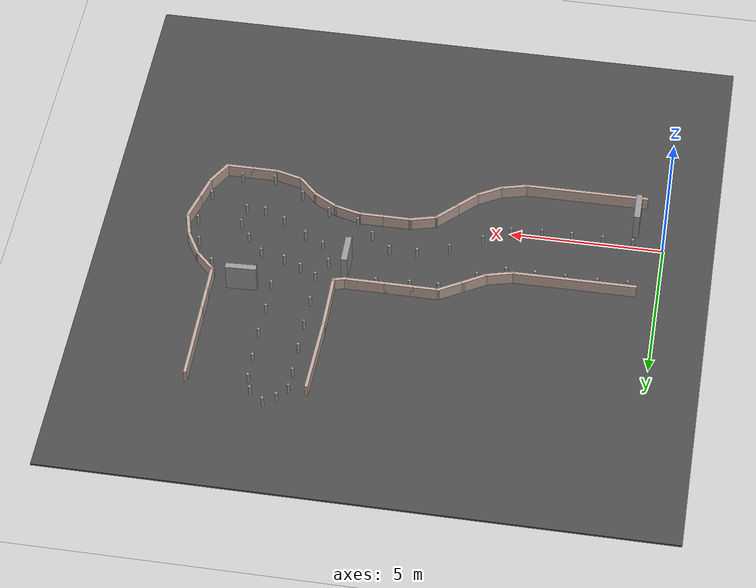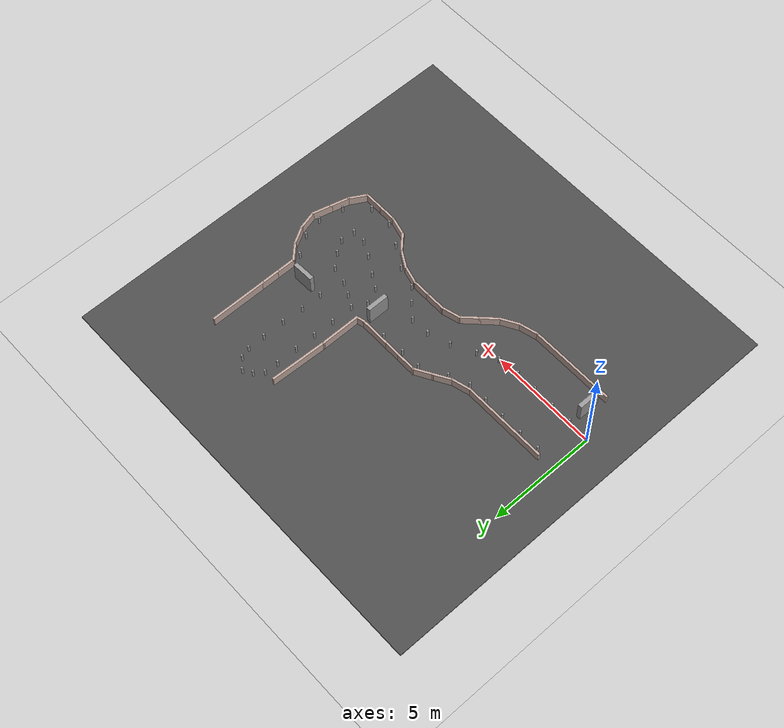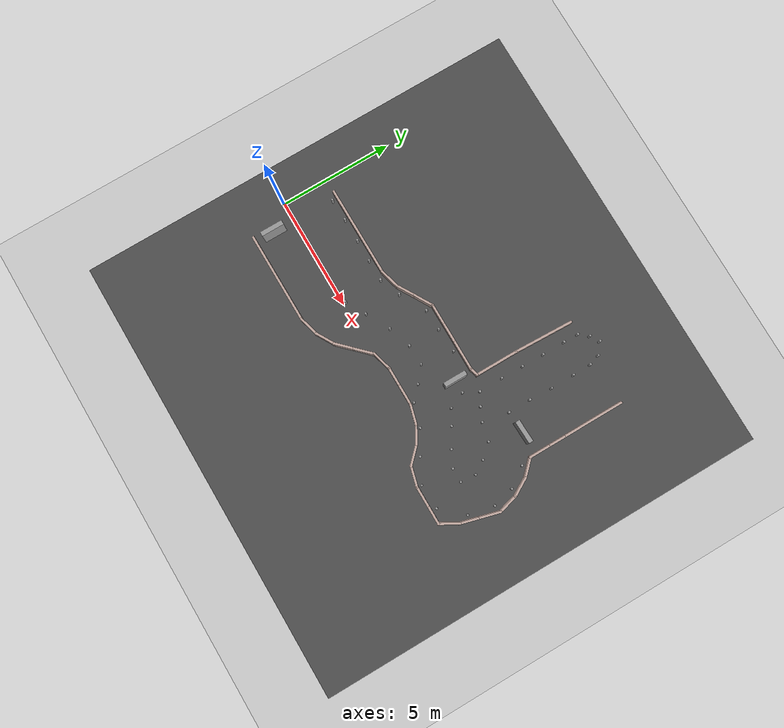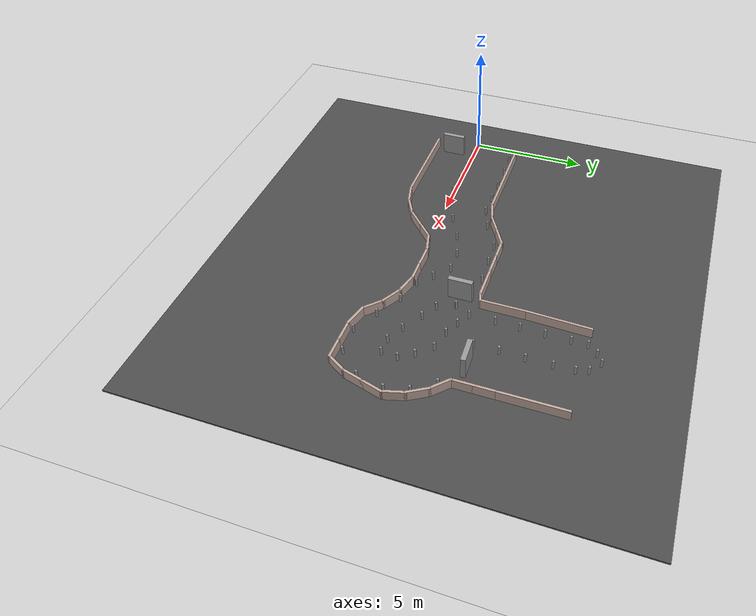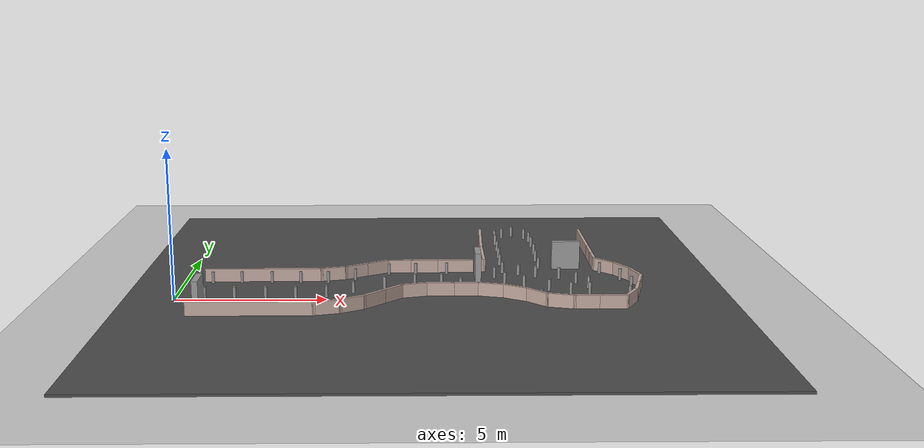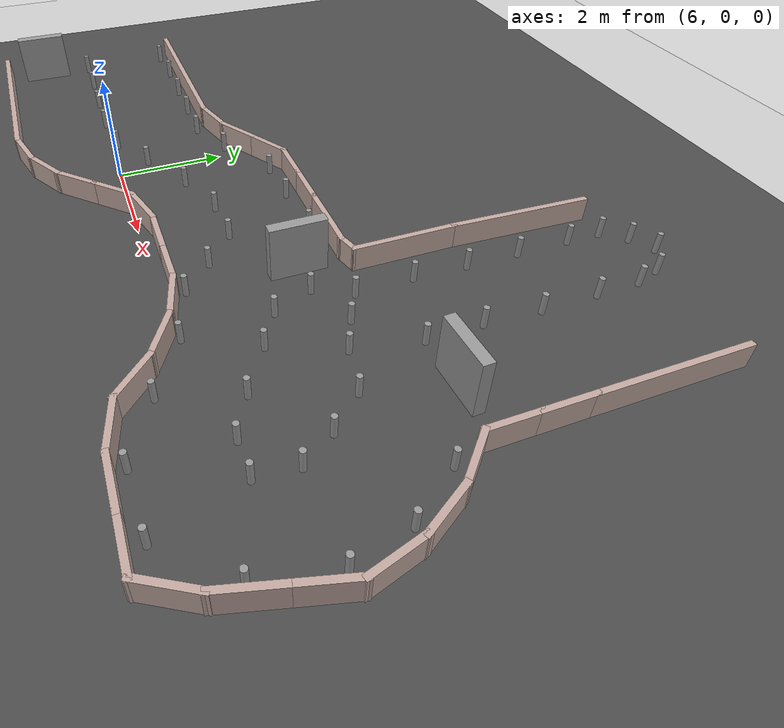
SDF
<sdf version="1.7">
 <world name="default">
  <light name="sun" type="directional">
   <pose>0 0 10 0 -0 0</pose>
   <diffuse>0.8 0.8 0.8 1</diffuse>
   <specular>0.2 0.2 0.2 1</specular>
   <attenuation>
    <range>1000</range>
    <constant>0.9</constant>
    <linear>0.01</linear>
    <quadratic>0.001</quadratic>
   </attenuation>
   <direction>-0.5 0.1 -0.9</direction>
   <spot><inner_angle>0</inner_angle><outer_angle>0</outer_angle><falloff>0</falloff></spot>
  </light>
  <model name="ground_plane">
   <static>1</static>
   <link name="link">
    <collision name="collision">
     <geometry><plane><normal>0 0 1</normal><size>100 100</size></plane></geometry>
     <surface>
      <contact><collide_bitmask>65535</collide_bitmask></contact>
      <friction><ode><mu>100</mu><mu2>50</mu2></ode></friction>
     </surface>
    </collision>
    <visual name="visual">
     <cast_shadows>0</cast_shadows>
     <geometry><plane><normal>0 0 1</normal><size>100 100</size></plane></geometry>
     <material>
      <script><uri>file://media/materials/scripts/gazebo.material</uri><name>Gazebo/Grey</name></script>
     </material>
    </visual>
   </link>
  </model>
  <gravity>0 0 -9.8</gravity>
  <magnetic_field>6e-06 2.3e-05 -4.2e-05</magnetic_field>
  <atmosphere type="adiabatic"/>
  <physics type="ode">
   <max_step_size>0.001</max_step_size>
   <real_time_factor>1</real_time_factor>
   <real_time_update_rate>1000</real_time_update_rate>
  </physics>
  <scene><ambient>0.4 0.4 0.4 1</ambient><background>0.7 0.7 0.7 1</background><shadows>1</shadows></scene>
  <spherical_coordinates>
   <surface_model>EARTH_WGS84</surface_model>
   <latitude_deg>0</latitude_deg>
   <longitude_deg>0</longitude_deg>
   <elevation>0</elevation>
   <heading_deg>0</heading_deg>
  </spherical_coordinates>
  <model name="Autonomous">
   <pose>8.14492 2.90909 0 0 -0 0</pose>
   <link name="Wall_0">
    <collision name="Wall_0_Collision">
     <geometry><box><size>4.0805 0.1 0.5</size></box></geometry>
     <pose>0 0 0.25 0 -0 0</pose>
    </collision>
    <visual name="Wall_0_Visual">
     <pose>0 0 0.25 0 -0 0</pose>
     <geometry><box><size>4.0805 0.1 0.5</size></box></geometry>
     <material>
      <script><uri>file://media/materials/scripts/gazebo.material</uri><name>Gazebo/Grey</name></script>
      <ambient>0.760784 0.662745 0.627451 1</ambient>
     </material>
     <meta><layer>0</layer></meta>
    </visual>
    <pose>-5.41802 -4.7193 0 0 -0 0.005053</pose>
   </link>
   <link name="Wall_10">
    <collision name="Wall_10_Collision">
     <geometry><box><size>0.95 0.1 0.5</size></box></geometry>
     <pose>0 0 0.25 0 -0 0</pose>
    </collision>
    <visual name="Wall_10_Visual">
     <pose>0 0 0.25 0 -0 0</pose>
     <geometry><box><size>0.95 0.1 0.5</size></box></geometry>
     <material>
      <script><uri>file://media/materials/scripts/gazebo.material</uri><name>Gazebo/Grey</name></script>
      <ambient>0.760784 0.662745 0.627451 1</ambient>
     </material>
     <meta><layer>0</layer></meta>
    </visual>
    <pose>1.42721 -2.64224 0 0 -0 0</pose>
   </link>
   <link name="Wall_11">
    <collision name="Wall_11_Collision">
     <geometry><box><size>0.950248 0.1 0.5</size></box></geometry>
     <pose>0 0 0.25 0 -0 0</pose>
    </collision>
    <visual name="Wall_11_Visual">
     <pose>0 0 0.25 0 -0 0</pose>
     <geometry><box><size>0.950248 0.1 0.5</size></box></geometry>
     <material>
      <script><uri>file://media/materials/scripts/gazebo.material</uri><name>Gazebo/Grey</name></script>
      <ambient>0.760784 0.662745 0.627451 1</ambient>
     </material>
     <meta><layer>0</layer></meta>
    </visual>
    <pose>2.26271 -2.75224 0 0 -0 -0.261815</pose>
   </link>
   <link name="Wall_12">
    <collision name="Wall_12_Collision">
     <geometry><box><size>0.950233 0.1 0.5</size></box></geometry>
     <pose>0 0 0.25 0 -0 0</pose>
    </collision>
    <visual name="Wall_12_Visual">
     <pose>0 0 0.25 0 -0 0</pose>
     <geometry><box><size>0.950233 0.1 0.5</size></box></geometry>
     <material>
      <script><uri>file://media/materials/scripts/gazebo.material</uri><name>Gazebo/Grey</name></script>
      <ambient>0.760784 0.662745 0.627451 1</ambient>
     </material>
     <meta><layer>0</layer></meta>
    </visual>
    <pose>3.04121 -3.07474 0 0 -0 -0.52367</pose>
   </link>
   <link name="Wall_13">
    <collision name="Wall_13_Collision">
     <geometry><box><size>0.950253 0.1 0.5</size></box></geometry>
     <pose>0 0 0.25 0 -0 0</pose>
    </collision>
    <visual name="Wall_13_Visual">
     <pose>0 0 0.25 0 -0 0</pose>
     <geometry><box><size>0.950253 0.1 0.5</size></box></geometry>
     <material>
      <script><uri>file://media/materials/scripts/gazebo.material</uri><name>Gazebo/Grey</name></script>
      <ambient>0.760784 0.662745 0.627451 1</ambient>
     </material>
     <meta><layer>0</layer></meta>
    </visual>
    <pose>3.70971 -3.58774 0 0 -0 -0.785398</pose>
   </link>
   <link name="Wall_14">
    <collision name="Wall_14_Collision">
     <geometry><box><size>0.970267 0.1 0.5</size></box></geometry>
     <pose>0 0 0.25 0 -0 0</pose>
    </collision>
    <visual name="Wall_14_Visual">
     <pose>0 0 0.25 0 -0 0</pose>
     <geometry><box><size>0.970267 0.1 0.5</size></box></geometry>
     <material>
      <script><uri>file://media/materials/scripts/gazebo.material</uri><name>Gazebo/Grey</name></script>
      <ambient>0.760784 0.662745 0.627451 1</ambient>
     </material>
     <meta><layer>0</layer></meta>
    </visual>
    <pose>4.43121 -3.99824 0 0 -0 -0.255569</pose>
   </link>
   <link name="Wall_15">
    <collision name="Wall_15_Collision">
     <geometry><box><size>0.949627 0.1 0.5</size></box></geometry>
     <pose>0 0 0.25 0 -0 0</pose>
    </collision>
    <visual name="Wall_15_Visual">
     <pose>0 0 0.25 0 -0 0</pose>
     <geometry><box><size>0.949627 0.1 0.5</size></box></geometry>
     <material>
      <script><uri>file://media/materials/scripts/gazebo.material</uri><name>Gazebo/Grey</name></script>
      <ambient>0.760784 0.662745 0.627451 1</ambient>
     </material>
     <meta><layer>0</layer></meta>
    </visual>
    <pose>5.27721 -4.10824 0 0 -0 0</pose>
   </link>
   <link name="Wall_16">
    <collision name="Wall_16_Collision">
     <geometry><box><size>0.929513 0.1 0.5</size></box></geometry>
     <pose>0 0 0.25 0 -0 0</pose>
    </collision>
    <visual name="Wall_16_Visual">
     <pose>0 0 0.25 0 -0 0</pose>
     <geometry><box><size>0.929513 0.1 0.5</size></box></geometry>
     <material>
      <script><uri>file://media/materials/scripts/gazebo.material</uri><name>Gazebo/Grey</name></script>
      <ambient>0.760784 0.662745 0.627451 1</ambient>
     </material>
     <meta><layer>0</layer></meta>
    </visual>
    <pose>6.11721 -4.10824 0 0 -0 0</pose>
   </link>
   <link name="Wall_18">
    <collision name="Wall_18_Collision">
     <geometry><box><size>0.949792 0.1 0.5</size></box></geometry>
     <pose>0 0 0.25 0 -0 0</pose>
    </collision>
    <visual name="Wall_18_Visual">
     <pose>0 0 0.25 0 -0 0</pose>
     <geometry><box><size>0.949792 0.1 0.5</size></box></geometry>
     <material>
      <script><uri>file://media/materials/scripts/gazebo.material</uri><name>Gazebo/Grey</name></script>
      <ambient>0.760784 0.662745 0.627451 1</ambient>
     </material>
     <meta><layer>0</layer></meta>
    </visual>
    <pose>6.74471 -3.74024 0 0 -0 1.04713</pose>
   </link>
   <link name="Wall_19">
    <collision name="Wall_19_Collision">
     <geometry><box><size>0.950031 0.1 0.5</size></box></geometry>
     <pose>0 0 0.25 0 -0 0</pose>
    </collision>
    <visual name="Wall_19_Visual">
     <pose>0 0 0.25 0 -0 0</pose>
     <geometry><box><size>0.950031 0.1 0.5</size></box></geometry>
     <material>
      <script><uri>file://media/materials/scripts/gazebo.material</uri><name>Gazebo/Grey</name></script>
      <ambient>0.760784 0.662745 0.627451 1</ambient>
     </material>
     <meta><layer>0</layer></meta>
    </visual>
    <pose>7.06721 -2.96174 0 0 -0 1.30898</pose>
   </link>
   <link name="Wall_20">
    <collision name="Wall_20_Collision">
     <geometry><box><size>0.950066 0.1 0.5</size></box></geometry>
     <pose>0 0 0.25 0 -0 0</pose>
    </collision>
    <visual name="Wall_20_Visual">
     <pose>0 0 0.25 0 -0 0</pose>
     <geometry><box><size>0.950066 0.1 0.5</size></box></geometry>
     <material>
      <script><uri>file://media/materials/scripts/gazebo.material</uri><name>Gazebo/Grey</name></script>
      <ambient>0.760784 0.662745 0.627451 1</ambient>
     </material>
     <meta><layer>0</layer></meta>
    </visual>
    <pose>7.28721 -2.14074 0 0 -0 1.30898</pose>
   </link>
   <link name="Wall_21">
    <collision name="Wall_21_Collision">
     <geometry><box><size>0.950356 0.1 0.5</size></box></geometry>
     <pose>0 0 0.25 0 -0 0</pose>
    </collision>
    <visual name="Wall_21_Visual">
     <pose>0 0 0.25 0 -0 0</pose>
     <geometry><box><size>0.950356 0.1 0.5</size></box></geometry>
     <material>
      <script><uri>file://media/materials/scripts/gazebo.material</uri><name>Gazebo/Grey</name></script>
      <ambient>0.760784 0.662745 0.627451 1</ambient>
     </material>
     <meta><layer>0</layer></meta>
    </visual>
    <pose>7.28721 -1.31974 0 0 -0 1.83261</pose>
   </link>
   <link name="Wall_22">
    <collision name="Wall_22_Collision">
     <geometry><box><size>0.950482 0.1 0.5</size></box></geometry>
     <pose>0 0 0.25 0 -0 0</pose>
    </collision>
    <visual name="Wall_22_Visual">
     <pose>0 0 0.25 0 -0 0</pose>
     <geometry><box><size>0.950482 0.1 0.5</size></box></geometry>
     <material>
      <script><uri>file://media/materials/scripts/gazebo.material</uri><name>Gazebo/Grey</name></script>
      <ambient>0.760784 0.662745 0.627451 1</ambient>
     </material>
     <meta><layer>0</layer></meta>
    </visual>
    <pose>6.96471 -0.54124 0 0 -0 2.09447</pose>
   </link>
   <link name="Wall_23">
    <collision name="Wall_23_Collision">
     <geometry><box><size>0.950626 0.1 0.5</size></box></geometry>
     <pose>0 0 0.25 0 -0 0</pose>
    </collision>
    <visual name="Wall_23_Visual">
     <pose>0 0 0.25 0 -0 0</pose>
     <geometry><box><size>0.950626 0.1 0.5</size></box></geometry>
     <material>
      <script><uri>file://media/materials/scripts/gazebo.material</uri><name>Gazebo/Grey</name></script>
      <ambient>0.760784 0.662745 0.627451 1</ambient>
     </material>
     <meta><layer>0</layer></meta>
    </visual>
    <pose>6.45121 0.12726 0 0 -0 2.35703</pose>
   </link>
   <link name="Wall_25">
    <collision name="Wall_25_Collision">
     <geometry><box><size>0.950436 0.1 0.5</size></box></geometry>
     <pose>0 0 0.25 0 -0 0</pose>
    </collision>
    <visual name="Wall_25_Visual">
     <pose>0 0 0.25 0 -0 0</pose>
     <geometry><box><size>0.950436 0.1 0.5</size></box></geometry>
     <material>
      <script><uri>file://media/materials/scripts/gazebo.material</uri><name>Gazebo/Grey</name></script>
      <ambient>0.760784 0.662745 0.627451 1</ambient>
     </material>
     <meta><layer>0</layer></meta>
    </visual>
    <pose>6.15021 0.85276 0 0 -0 1.5708</pose>
   </link>
   <link name="Wall_26">
    <collision name="Wall_26_Collision">
     <geometry><box><size>0.950436 0.1 0.5</size></box></geometry>
     <pose>0 0 0.25 0 -0 0</pose>
    </collision>
    <visual name="Wall_26_Visual">
     <pose>0 0 0.25 0 -0 0</pose>
     <geometry><box><size>0.950436 0.1 0.5</size></box></geometry>
     <material>
      <script><uri>file://media/materials/scripts/gazebo.material</uri><name>Gazebo/Grey</name></script>
      <ambient>0.760784 0.662745 0.627451 1</ambient>
     </material>
     <meta><layer>0</layer></meta>
    </visual>
    <pose>6.15021 1.70276 0 0 -0 1.5708</pose>
   </link>
   <link name="Wall_3">
    <collision name="Wall_3_Collision">
     <geometry><box><size>0.95 0.1 0.5</size></box></geometry>
     <pose>0 0 0.25 0 -0 0</pose>
    </collision>
    <visual name="Wall_3_Visual">
     <pose>0 0 0.25 0 -0 0</pose>
     <geometry><box><size>0.95 0.1 0.5</size></box></geometry>
     <material>
      <script><uri>file://media/materials/scripts/gazebo.material</uri><name>Gazebo/Grey</name></script>
      <ambient>0.760784 0.662745 0.627451 1</ambient>
     </material>
     <meta><layer>0</layer></meta>
    </visual>
    <pose>-3.01729 -4.59924 0 0 -0 0.261815</pose>
   </link>
   <link name="Wall_31">
    <collision name="Wall_31_Collision">
     <geometry><box><size>4.05051 0.1 0.5</size></box></geometry>
     <pose>0 0 0.25 0 -0 0</pose>
    </collision>
    <visual name="Wall_31_Visual">
     <pose>0 0 0.25 0 -0 0</pose>
     <geometry><box><size>4.05051 0.1 0.5</size></box></geometry>
     <material>
      <script><uri>file://media/materials/scripts/gazebo.material</uri><name>Gazebo/Grey</name></script>
      <ambient>0.760784 0.662745 0.627451 1</ambient>
     </material>
     <meta><layer>0</layer></meta>
    </visual>
    <pose>-5.43302 -0.869297 0 0 -0 0.005091</pose>
   </link>
   <link name="Wall_32">
    <collision name="Wall_32_Collision">
     <geometry><box><size>0.950075 0.1 0.5</size></box></geometry>
     <pose>0 0 0.25 0 -0 0</pose>
    </collision>
    <visual name="Wall_32_Visual">
     <pose>0 0 0.25 0 -0 0</pose>
     <geometry><box><size>0.950075 0.1 0.5</size></box></geometry>
     <material>
      <script><uri>file://media/materials/scripts/gazebo.material</uri><name>Gazebo/Grey</name></script>
      <ambient>0.760784 0.662745 0.627451 1</ambient>
     </material>
     <meta><layer>0</layer></meta>
    </visual>
    <pose>-3.04729 -0.74924 0 0 -0 0.261815</pose>
   </link>
   <link name="Wall_33">
    <collision name="Wall_33_Collision">
     <geometry><box><size>0.932635 0.1 0.5</size></box></geometry>
     <pose>0 0 0.25 0 -0 0</pose>
    </collision>
    <visual name="Wall_33_Visual">
     <pose>0 0 0.25 0 -0 0</pose>
     <geometry><box><size>0.932635 0.1 0.5</size></box></geometry>
     <material>
      <script><uri>file://media/materials/scripts/gazebo.material</uri><name>Gazebo/Grey</name></script>
      <ambient>0.760784 0.662745 0.627451 1</ambient>
     </material>
     <meta><layer>0</layer></meta>
    </visual>
    <pose>-2.27879 -0.42674 0 0 -0 0.535682</pose>
   </link>
   <link name="Wall_34">
    <collision name="Wall_34_Collision">
     <geometry><box><size>0.949895 0.1 0.5</size></box></geometry>
     <pose>0 0 0.25 0 -0 0</pose>
    </collision>
    <visual name="Wall_34_Visual">
     <pose>0 0 0.25 0 -0 0</pose>
     <geometry><box><size>0.949895 0.1 0.5</size></box></geometry>
     <material>
      <script><uri>file://media/materials/scripts/gazebo.material</uri><name>Gazebo/Grey</name></script>
      <ambient>0.760784 0.662745 0.627451 1</ambient>
     </material>
     <meta><layer>0</layer></meta>
    </visual>
    <pose>-1.55279 -0.00174 0 0 -0 0.52367</pose>
   </link>
   <link name="Wall_35">
    <collision name="Wall_35_Collision">
     <geometry><box><size>0.95 0.1 0.5</size></box></geometry>
     <pose>0 0 0.25 0 -0 0</pose>
    </collision>
    <visual name="Wall_35_Visual">
     <pose>0 0 0.25 0 -0 0</pose>
     <geometry><box><size>0.95 0.1 0.5</size></box></geometry>
     <material>
      <script><uri>file://media/materials/scripts/gazebo.material</uri><name>Gazebo/Grey</name></script>
      <ambient>0.760784 0.662745 0.627451 1</ambient>
     </material>
     <meta><layer>0</layer></meta>
    </visual>
    <pose>-0.75979 0.21076 0 0 -0 0</pose>
   </link>
   <link name="Wall_36">
    <collision name="Wall_36_Collision">
     <geometry><box><size>0.95 0.1 0.5</size></box></geometry>
     <pose>0 0 0.25 0 -0 0</pose>
    </collision>
    <visual name="Wall_36_Visual">
     <pose>0 0 0.25 0 -0 0</pose>
     <geometry><box><size>0.95 0.1 0.5</size></box></geometry>
     <material>
      <script><uri>file://media/materials/scripts/gazebo.material</uri><name>Gazebo/Grey</name></script>
      <ambient>0.760784 0.662745 0.627451 1</ambient>
     </material>
     <meta><layer>0</layer></meta>
    </visual>
    <pose>0.09021 0.21076 0 0 -0 0</pose>
   </link>
   <link name="Wall_4">
    <collision name="Wall_4_Collision">
     <geometry><box><size>0.95003 0.1 0.5</size></box></geometry>
     <pose>0 0 0.25 0 -0 0</pose>
    </collision>
    <visual name="Wall_4_Visual">
     <pose>0 0 0.25 0 -0 0</pose>
     <geometry><box><size>0.95003 0.1 0.5</size></box></geometry>
     <material>
      <script><uri>file://media/materials/scripts/gazebo.material</uri><name>Gazebo/Grey</name></script>
      <ambient>0.760784 0.662745 0.627451 1</ambient>
     </material>
     <meta><layer>0</layer></meta>
    </visual>
    <pose>-2.23879 -4.27674 0 0 -0 0.52367</pose>
   </link>
   <link name="Wall_42">
    <collision name="Wall_42_Collision">
     <geometry><box><size>1.45 0.1 0.5</size></box></geometry>
     <pose>0 0 0.25 0 -0 0</pose>
    </collision>
    <visual name="Wall_42_Visual">
     <pose>0 0 0.25 0 -0 0</pose>
     <geometry><box><size>1.45 0.1 0.5</size></box></geometry>
     <material>
      <script><uri>file://media/materials/scripts/gazebo.material</uri><name>Gazebo/Grey</name></script>
      <ambient>0.760784 0.662745 0.627451 1</ambient>
     </material>
     <meta><layer>0</layer></meta>
    </visual>
    <pose>1.19021 0.21076 0 0 -0 0</pose>
   </link>
   <link name="Wall_45">
    <collision name="Wall_45_Collision">
     <geometry><box><size>0.450036 0.1 0.5</size></box></geometry>
     <pose>0 0 0.25 0 -0 0</pose>
    </collision>
    <visual name="Wall_45_Visual">
     <pose>0 0 0.25 0 -0 0</pose>
     <geometry><box><size>0.450036 0.1 0.5</size></box></geometry>
     <material>
      <script><uri>file://media/materials/scripts/gazebo.material</uri><name>Gazebo/Grey</name></script>
      <ambient>0.760784 0.662745 0.627451 1</ambient>
     </material>
     <meta><layer>0</layer></meta>
    </visual>
    <pose>2.03421 0.25626 0 0 -0 0.262995</pose>
   </link>
   <link name="Wall_46">
    <collision name="Wall_46_Collision">
     <geometry><box><size>1.94958 0.1 0.5</size></box></geometry>
     <pose>0 0 0.25 0 -0 0</pose>
    </collision>
    <visual name="Wall_46_Visual">
     <pose>0 0 0.25 0 -0 0</pose>
     <geometry><box><size>1.94958 0.1 0.5</size></box></geometry>
     <material>
      <script><uri>file://media/materials/scripts/gazebo.material</uri><name>Gazebo/Grey</name></script>
      <ambient>0.760784 0.662745 0.627451 1</ambient>
     </material>
     <meta><layer>0</layer></meta>
    </visual>
    <pose>2.20321 1.22676 0 0 -0 1.5708</pose>
   </link>
   <link name="Wall_48">
    <collision name="Wall_48_Collision">
     <geometry><box><size>2.7 0.1 0.5</size></box></geometry>
     <pose>0 0 0.25 0 -0 0</pose>
    </collision>
    <visual name="Wall_48_Visual">
     <pose>0 0 0.25 0 -0 0</pose>
     <geometry><box><size>2.7 0.1 0.5</size></box></geometry>
     <material>
      <script><uri>file://media/materials/scripts/gazebo.material</uri><name>Gazebo/Grey</name></script>
      <ambient>0.760784 0.662745 0.627451 1</ambient>
     </material>
     <meta><layer>0</layer></meta>
    </visual>
    <pose>6.15021 3.42776 0 0 -0 1.5708</pose>
   </link>
   <link name="Wall_5">
    <collision name="Wall_5_Collision">
     <geometry><box><size>0.950109 0.1 0.5</size></box></geometry>
     <pose>0 0 0.25 0 -0 0</pose>
    </collision>
    <visual name="Wall_5_Visual">
     <pose>0 0 0.25 0 -0 0</pose>
     <geometry><box><size>0.950109 0.1 0.5</size></box></geometry>
     <material>
      <script><uri>file://media/materials/scripts/gazebo.material</uri><name>Gazebo/Grey</name></script>
      <ambient>0.760784 0.662745 0.627451 1</ambient>
     </material>
     <meta><layer>0</layer></meta>
    </visual>
    <pose>-1.57029 -3.76374 0 0 -0 0.785398</pose>
   </link>
   <link name="Wall_54">
    <collision name="Wall_54_Collision">
     <geometry><box><size>2.67783 0.1 0.5</size></box></geometry>
     <pose>0 0 0.25 0 -0 0</pose>
    </collision>
    <visual name="Wall_54_Visual">
     <pose>0 0 0.25 0 -0 0</pose>
     <geometry><box><size>2.67783 0.1 0.5</size></box></geometry>
     <material>
      <script><uri>file://media/materials/scripts/gazebo.material</uri><name>Gazebo/Grey</name></script>
      <ambient>0.760784 0.662745 0.627451 1</ambient>
     </material>
     <meta><layer>0</layer></meta>
    </visual>
    <pose>2.25171 3.43976 0 0 -0 -1.60843</pose>
   </link>
   <link name="Wall_6">
    <collision name="Wall_6_Collision">
     <geometry><box><size>0.950167 0.1 0.5</size></box></geometry>
     <pose>0 0 0.25 0 -0 0</pose>
    </collision>
    <visual name="Wall_6_Visual">
     <pose>0 0 0.25 0 -0 0</pose>
     <geometry><box><size>0.950167 0.1 0.5</size></box></geometry>
     <material>
      <script><uri>file://media/materials/scripts/gazebo.material</uri><name>Gazebo/Grey</name></script>
      <ambient>0.760784 0.662745 0.627451 1</ambient>
     </material>
     <meta><layer>0</layer></meta>
    </visual>
    <pose>-0.96929 -3.16274 0 0 -0 0.785398</pose>
   </link>
   <link name="Wall_7">
    <collision name="Wall_7_Collision">
     <geometry><box><size>0.950252 0.1 0.5</size></box></geometry>
     <pose>0 0 0.25 0 -0 0</pose>
    </collision>
    <visual name="Wall_7_Visual">
     <pose>0 0 0.25 0 -0 0</pose>
     <geometry><box><size>0.950252 0.1 0.5</size></box></geometry>
     <material>
      <script><uri>file://media/materials/scripts/gazebo.material</uri><name>Gazebo/Grey</name></script>
      <ambient>0.760784 0.662745 0.627451 1</ambient>
     </material>
     <meta><layer>0</layer></meta>
    </visual>
    <pose>-0.25829 -2.75224 0 0 -0 0.261815</pose>
   </link>
   <link name="Wall_8">
    <collision name="Wall_8_Collision">
     <geometry><box><size>0.950277 0.1 0.5</size></box></geometry>
     <pose>0 0 0.25 0 -0 0</pose>
    </collision>
    <visual name="Wall_8_Visual">
     <pose>0 0 0.25 0 -0 0</pose>
     <geometry><box><size>0.950277 0.1 0.5</size></box></geometry>
     <material>
      <script><uri>file://media/materials/scripts/gazebo.material</uri><name>Gazebo/Grey</name></script>
      <ambient>0.760784 0.662745 0.627451 1</ambient>
     </material>
     <meta><layer>0</layer></meta>
    </visual>
    <pose>0.57721 -2.64224 0 0 -0 0</pose>
   </link>
   <static>1</static>
  </model>
  <model name="Cone">
   <link name="link_1">
    <inertial>
     <mass>1</mass>
     <inertia><ixx>0.145833</ixx><ixy>0</ixy><ixz>0</ixz><iyy>0.145833</iyy><iyz>0</iyz><izz>0.125</izz></inertia>
    </inertial>
    <visual name="visual">
     <geometry><cylinder><radius>0.05</radius><length>0.4</length></cylinder></geometry>
     <material>
      <lighting>1</lighting>
      <script><uri>file://media/materials/scripts/gazebo.material</uri><name>Gazebo/Grey</name></script>
      <shader type="pixel"><normal_map>__default__</normal_map></shader>
      <ambient>1 1 1 1</ambient>
      <diffuse>1 1 1 1</diffuse>
      <specular>0.01 0.01 0.01 1</specular>
      <emissive>0 0 0 1</emissive>
     </material>
    </visual>
    <collision name="collision">
     <geometry><cylinder><radius>0.05</radius><length>0.4</length></cylinder></geometry>
     <surface>
      <friction>
       <ode><mu>1</mu><mu2>1</mu2><fdir1>0 0 0</fdir1><slip1>0</slip1><slip2>0</slip2></ode>
       <torsional>
        <coefficient>1</coefficient>
        <patch_radius>0</patch_radius>
        <surface_radius>0</surface_radius>
        <use_patch_radius>1</use_patch_radius>
        <ode><slip>0</slip></ode>
       </torsional>
      </friction>
      <bounce><restitution_coefficient>0</restitution_coefficient><threshold>1e+06</threshold></bounce>
      <contact>
       <collide_without_contact>0</collide_without_contact>
       <collide_without_contact_bitmask>1</collide_without_contact_bitmask>
       <collide_bitmask>1</collide_bitmask>
       <ode>
        <soft_cfm>0</soft_cfm>
        <soft_erp>0.2</soft_erp>
        <kp>1e+13</kp>
        <kd>1</kd>
        <max_vel>0.01</max_vel>
        <min_depth>0</min_depth>
       </ode>
       <bullet>
        <split_impulse>1</split_impulse>
        <split_impulse_penetration_threshold>-0.01</split_impulse_penetration_threshold>
        <soft_cfm>0</soft_cfm>
        <soft_erp>0.2</soft_erp>
        <kp>1e+13</kp>
        <kd>1</kd>
       </bullet>
      </contact>
     </surface>
    </collision>
   </link>
   <static>0</static>
   <pose>0.999771 7e-05 0.249999 -2.9e-05 6.5e-05 -0.000279</pose>
  </model>
  <model name="Obstacle">
   <link name="link_4">
    <inertial>
     <mass>1</mass>
     <inertia>
      <ixx>0.166667</ixx>
      <ixy>0</ixy>
      <ixz>0</ixz>
      <iyy>0.166667</iyy>
      <iyz>0</iyz>
      <izz>0.166667</izz>
     </inertia>
    </inertial>
    <visual name="visual">
     <geometry><box><size>0.2 1 1</size></box></geometry>
     <material>
      <lighting>1</lighting>
      <script><uri>file://media/materials/scripts/gazebo.material</uri><name>Gazebo/Grey</name></script>
      <shader type="pixel"><normal_map>__default__</normal_map></shader>
      <ambient>0 0 0 1</ambient>
      <diffuse>0 0 0 1</diffuse>
      <specular>0.01 0.01 0.01 1</specular>
      <emissive>0 0 0 1</emissive>
     </material>
    </visual>
    <collision name="collision">
     <geometry><box><size>0.2 1 1</size></box></geometry>
     <surface>
      <friction>
       <ode><mu>1</mu><mu2>1</mu2><fdir1>0 0 0</fdir1><slip1>0</slip1><slip2>0</slip2></ode>
       <torsional>
        <coefficient>1</coefficient>
        <patch_radius>0</patch_radius>
        <surface_radius>0</surface_radius>
        <use_patch_radius>1</use_patch_radius>
        <ode><slip>0</slip></ode>
       </torsional>
      </friction>
      <bounce><restitution_coefficient>0</restitution_coefficient><threshold>1e+06</threshold></bounce>
      <contact>
       <collide_without_contact>0</collide_without_contact>
       <collide_without_contact_bitmask>1</collide_without_contact_bitmask>
       <collide_bitmask>1</collide_bitmask>
       <ode>
        <soft_cfm>0</soft_cfm>
        <soft_erp>0.2</soft_erp>
        <kp>1e+13</kp>
        <kd>1</kd>
        <max_vel>0.01</max_vel>
        <min_depth>0</min_depth>
       </ode>
       <bullet>
        <split_impulse>1</split_impulse>
        <split_impulse_penetration_threshold>-0.01</split_impulse_penetration_threshold>
        <soft_cfm>0</soft_cfm>
        <soft_erp>0.2</soft_erp>
        <kp>1e+13</kp>
        <kd>1</kd>
       </bullet>
      </contact>
     </surface>
    </collision>
   </link>
   <static>0</static>
   <pose>0.955546 -0.96149 0.55 0 0 -6e-06</pose>
  </model>
  <model name="Cone_clone">
   <link name="link_1">
    <inertial>
     <mass>1</mass>
     <inertia><ixx>0.145833</ixx><ixy>0</ixy><ixz>0</ixz><iyy>0.145833</iyy><iyz>0</iyz><izz>0.125</izz></inertia>
    </inertial>
    <visual name="visual">
     <geometry><cylinder><radius>0.05</radius><length>0.4</length></cylinder></geometry>
     <material>
      <lighting>1</lighting>
      <script><uri>file://media/materials/scripts/gazebo.material</uri><name>Gazebo/Grey</name></script>
      <shader type="pixel"><normal_map>__default__</normal_map></shader>
      <ambient>1 1 1 1</ambient>
      <diffuse>1 1 1 1</diffuse>
      <specular>0.01 0.01 0.01 1</specular>
      <emissive>0 0 0 1</emissive>
     </material>
    </visual>
    <collision name="collision">
     <geometry><cylinder><radius>0.05</radius><length>0.4</length></cylinder></geometry>
     <surface>
      <friction>
       <ode><mu>1</mu><mu2>1</mu2><fdir1>0 0 0</fdir1><slip1>0</slip1><slip2>0</slip2></ode>
       <torsional>
        <coefficient>1</coefficient>
        <patch_radius>0</patch_radius>
        <surface_radius>0</surface_radius>
        <use_patch_radius>1</use_patch_radius>
        <ode><slip>0</slip></ode>
       </torsional>
      </friction>
      <bounce><restitution_coefficient>0</restitution_coefficient><threshold>1e+06</threshold></bounce>
      <contact>
       <collide_without_contact>0</collide_without_contact>
       <collide_without_contact_bitmask>1</collide_without_contact_bitmask>
       <collide_bitmask>1</collide_bitmask>
       <ode>
        <soft_cfm>0</soft_cfm>
        <soft_erp>0.2</soft_erp>
        <kp>1e+13</kp>
        <kd>1</kd>
        <max_vel>0.01</max_vel>
        <min_depth>0</min_depth>
       </ode>
       <bullet>
        <split_impulse>1</split_impulse>
        <split_impulse_penetration_threshold>-0.01</split_impulse_penetration_threshold>
        <soft_cfm>0</soft_cfm>
        <soft_erp>0.2</soft_erp>
        <kp>1e+13</kp>
        <kd>1</kd>
       </bullet>
      </contact>
     </surface>
    </collision>
   </link>
   <static>0</static>
   <pose>0.9838 1.80334 0.249999 -2.8e-05 6.4e-05 -0.000282</pose>
  </model>
  <model name="Cone_clone_0">
   <link name="link_1">
    <inertial>
     <mass>1</mass>
     <inertia><ixx>0.145833</ixx><ixy>0</ixy><ixz>0</ixz><iyy>0.145833</iyy><iyz>0</iyz><izz>0.125</izz></inertia>
    </inertial>
    <visual name="visual">
     <geometry><cylinder><radius>0.05</radius><length>0.4</length></cylinder></geometry>
     <material>
      <lighting>1</lighting>
      <script><uri>file://media/materials/scripts/gazebo.material</uri><name>Gazebo/Grey</name></script>
      <shader type="pixel"><normal_map>__default__</normal_map></shader>
      <ambient>1 1 1 1</ambient>
      <diffuse>1 1 1 1</diffuse>
      <specular>0.01 0.01 0.01 1</specular>
      <emissive>0 0 0 1</emissive>
     </material>
    </visual>
    <collision name="collision">
     <geometry><cylinder><radius>0.05</radius><length>0.4</length></cylinder></geometry>
     <surface>
      <friction>
       <ode><mu>1</mu><mu2>1</mu2><fdir1>0 0 0</fdir1><slip1>0</slip1><slip2>0</slip2></ode>
       <torsional>
        <coefficient>1</coefficient>
        <patch_radius>0</patch_radius>
        <surface_radius>0</surface_radius>
        <use_patch_radius>1</use_patch_radius>
        <ode><slip>0</slip></ode>
       </torsional>
      </friction>
      <bounce><restitution_coefficient>0</restitution_coefficient><threshold>1e+06</threshold></bounce>
      <contact>
       <collide_without_contact>0</collide_without_contact>
       <collide_without_contact_bitmask>1</collide_without_contact_bitmask>
       <collide_bitmask>1</collide_bitmask>
       <ode>
        <soft_cfm>0</soft_cfm>
        <soft_erp>0.2</soft_erp>
        <kp>1e+13</kp>
        <kd>1</kd>
        <max_vel>0.01</max_vel>
        <min_depth>0</min_depth>
       </ode>
       <bullet>
        <split_impulse>1</split_impulse>
        <split_impulse_penetration_threshold>-0.01</split_impulse_penetration_threshold>
        <soft_cfm>0</soft_cfm>
        <soft_erp>0.2</soft_erp>
        <kp>1e+13</kp>
        <kd>1</kd>
       </bullet>
      </contact>
     </surface>
    </collision>
   </link>
   <static>0</static>
   <pose>1.97792 0.007597 0.249998 -2.7e-05 6e-05 -0.000282</pose>
  </model>
  <model name="Cone_clone_1">
   <link name="link_1">
    <inertial>
     <mass>1</mass>
     <inertia><ixx>0.145833</ixx><ixy>0</ixy><ixz>0</ixz><iyy>0.145833</iyy><iyz>0</iyz><izz>0.125</izz></inertia>
    </inertial>
    <visual name="visual">
     <geometry><cylinder><radius>0.05</radius><length>0.4</length></cylinder></geometry>
     <material>
      <lighting>1</lighting>
      <script><uri>file://media/materials/scripts/gazebo.material</uri><name>Gazebo/Grey</name></script>
      <shader type="pixel"><normal_map>__default__</normal_map></shader>
      <ambient>1 1 1 1</ambient>
      <diffuse>1 1 1 1</diffuse>
      <specular>0.01 0.01 0.01 1</specular>
      <emissive>0 0 0 1</emissive>
     </material>
    </visual>
    <collision name="collision">
     <geometry><cylinder><radius>0.05</radius><length>0.4</length></cylinder></geometry>
     <surface>
      <friction>
       <ode><mu>1</mu><mu2>1</mu2><fdir1>0 0 0</fdir1><slip1>0</slip1><slip2>0</slip2></ode>
       <torsional>
        <coefficient>1</coefficient>
        <patch_radius>0</patch_radius>
        <surface_radius>0</surface_radius>
        <use_patch_radius>1</use_patch_radius>
        <ode><slip>0</slip></ode>
       </torsional>
      </friction>
      <bounce><restitution_coefficient>0</restitution_coefficient><threshold>1e+06</threshold></bounce>
      <contact>
       <collide_without_contact>0</collide_without_contact>
       <collide_without_contact_bitmask>1</collide_without_contact_bitmask>
       <collide_bitmask>1</collide_bitmask>
       <ode>
        <soft_cfm>0</soft_cfm>
        <soft_erp>0.2</soft_erp>
        <kp>1e+13</kp>
        <kd>1</kd>
        <max_vel>0.01</max_vel>
        <min_depth>0</min_depth>
       </ode>
       <bullet>
        <split_impulse>1</split_impulse>
        <split_impulse_penetration_threshold>-0.01</split_impulse_penetration_threshold>
        <soft_cfm>0</soft_cfm>
        <soft_erp>0.2</soft_erp>
        <kp>1e+13</kp>
        <kd>1</kd>
       </bullet>
      </contact>
     </surface>
    </collision>
   </link>
   <static>0</static>
   <pose>3.00034 -0.001884 0.249999 -2.9e-05 6.4e-05 -0.000287</pose>
  </model>
  <model name="Cone_clone_2">
   <link name="link_1">
    <inertial>
     <mass>1</mass>
     <inertia><ixx>0.145833</ixx><ixy>0</ixy><ixz>0</ixz><iyy>0.145833</iyy><iyz>0</iyz><izz>0.125</izz></inertia>
    </inertial>
    <visual name="visual">
     <geometry><cylinder><radius>0.05</radius><length>0.4</length></cylinder></geometry>
     <material>
      <lighting>1</lighting>
      <script><uri>file://media/materials/scripts/gazebo.material</uri><name>Gazebo/Grey</name></script>
      <shader type="pixel"><normal_map>__default__</normal_map></shader>
      <ambient>1 1 1 1</ambient>
      <diffuse>1 1 1 1</diffuse>
      <specular>0.01 0.01 0.01 1</specular>
      <emissive>0 0 0 1</emissive>
     </material>
    </visual>
    <collision name="collision">
     <geometry><cylinder><radius>0.05</radius><length>0.4</length></cylinder></geometry>
     <surface>
      <friction>
       <ode><mu>1</mu><mu2>1</mu2><fdir1>0 0 0</fdir1><slip1>0</slip1><slip2>0</slip2></ode>
       <torsional>
        <coefficient>1</coefficient>
        <patch_radius>0</patch_radius>
        <surface_radius>0</surface_radius>
        <use_patch_radius>1</use_patch_radius>
        <ode><slip>0</slip></ode>
       </torsional>
      </friction>
      <bounce><restitution_coefficient>0</restitution_coefficient><threshold>1e+06</threshold></bounce>
      <contact>
       <collide_without_contact>0</collide_without_contact>
       <collide_without_contact_bitmask>1</collide_without_contact_bitmask>
       <collide_bitmask>1</collide_bitmask>
       <ode>
        <soft_cfm>0</soft_cfm>
        <soft_erp>0.2</soft_erp>
        <kp>1e+13</kp>
        <kd>1</kd>
        <max_vel>0.01</max_vel>
        <min_depth>0</min_depth>
       </ode>
       <bullet>
        <split_impulse>1</split_impulse>
        <split_impulse_penetration_threshold>-0.01</split_impulse_penetration_threshold>
        <soft_cfm>0</soft_cfm>
        <soft_erp>0.2</soft_erp>
        <kp>1e+13</kp>
        <kd>1</kd>
       </bullet>
      </contact>
     </surface>
    </collision>
   </link>
   <static>0</static>
   <pose>3.98344 0.005772 0.25 -3.7e-05 8.4e-05 5e-05</pose>
  </model>
  <model name="Cone_clone_3">
   <link name="link_1">
    <inertial>
     <mass>1</mass>
     <inertia><ixx>0.145833</ixx><ixy>0</ixy><ixz>0</ixz><iyy>0.145833</iyy><iyz>0</iyz><izz>0.125</izz></inertia>
    </inertial>
    <visual name="visual">
     <geometry><cylinder><radius>0.05</radius><length>0.4</length></cylinder></geometry>
     <material>
      <lighting>1</lighting>
      <script><uri>file://media/materials/scripts/gazebo.material</uri><name>Gazebo/Grey</name></script>
      <shader type="pixel"><normal_map>__default__</normal_map></shader>
      <ambient>1 1 1 1</ambient>
      <diffuse>1 1 1 1</diffuse>
      <specular>0.01 0.01 0.01 1</specular>
      <emissive>0 0 0 1</emissive>
     </material>
    </visual>
    <collision name="collision">
     <geometry><cylinder><radius>0.05</radius><length>0.4</length></cylinder></geometry>
     <surface>
      <friction>
       <ode><mu>1</mu><mu2>1</mu2><fdir1>0 0 0</fdir1><slip1>0</slip1><slip2>0</slip2></ode>
       <torsional>
        <coefficient>1</coefficient>
        <patch_radius>0</patch_radius>
        <surface_radius>0</surface_radius>
        <use_patch_radius>1</use_patch_radius>
        <ode><slip>0</slip></ode>
       </torsional>
      </friction>
      <bounce><restitution_coefficient>0</restitution_coefficient><threshold>1e+06</threshold></bounce>
      <contact>
       <collide_without_contact>0</collide_without_contact>
       <collide_without_contact_bitmask>1</collide_without_contact_bitmask>
       <collide_bitmask>1</collide_bitmask>
       <ode>
        <soft_cfm>0</soft_cfm>
        <soft_erp>0.2</soft_erp>
        <kp>1e+13</kp>
        <kd>1</kd>
        <max_vel>0.01</max_vel>
        <min_depth>0</min_depth>
       </ode>
       <bullet>
        <split_impulse>1</split_impulse>
        <split_impulse_penetration_threshold>-0.01</split_impulse_penetration_threshold>
        <soft_cfm>0</soft_cfm>
        <soft_erp>0.2</soft_erp>
        <kp>1e+13</kp>
        <kd>1</kd>
       </bullet>
      </contact>
     </surface>
    </collision>
   </link>
   <static>0</static>
   <pose>4.9866 0.112679 0.25 -4.7e-05 8.5e-05 1.4e-05</pose>
  </model>
  <model name="Cone_clone_4">
   <link name="link_1">
    <inertial>
     <mass>1</mass>
     <inertia><ixx>0.145833</ixx><ixy>0</ixy><ixz>0</ixz><iyy>0.145833</iyy><iyz>0</iyz><izz>0.125</izz></inertia>
    </inertial>
    <visual name="visual">
     <geometry><cylinder><radius>0.05</radius><length>0.4</length></cylinder></geometry>
     <material>
      <lighting>1</lighting>
      <script><uri>file://media/materials/scripts/gazebo.material</uri><name>Gazebo/Grey</name></script>
      <shader type="pixel"><normal_map>__default__</normal_map></shader>
      <ambient>1 1 1 1</ambient>
      <diffuse>1 1 1 1</diffuse>
      <specular>0.01 0.01 0.01 1</specular>
      <emissive>0 0 0 1</emissive>
     </material>
    </visual>
    <collision name="collision">
     <geometry><cylinder><radius>0.05</radius><length>0.4</length></cylinder></geometry>
     <surface>
      <friction>
       <ode><mu>1</mu><mu2>1</mu2><fdir1>0 0 0</fdir1><slip1>0</slip1><slip2>0</slip2></ode>
       <torsional>
        <coefficient>1</coefficient>
        <patch_radius>0</patch_radius>
        <surface_radius>0</surface_radius>
        <use_patch_radius>1</use_patch_radius>
        <ode><slip>0</slip></ode>
       </torsional>
      </friction>
      <bounce><restitution_coefficient>0</restitution_coefficient><threshold>1e+06</threshold></bounce>
      <contact>
       <collide_without_contact>0</collide_without_contact>
       <collide_without_contact_bitmask>1</collide_without_contact_bitmask>
       <collide_bitmask>1</collide_bitmask>
       <ode>
        <soft_cfm>0</soft_cfm>
        <soft_erp>0.2</soft_erp>
        <kp>1e+13</kp>
        <kd>1</kd>
        <max_vel>0.01</max_vel>
        <min_depth>0</min_depth>
       </ode>
       <bullet>
        <split_impulse>1</split_impulse>
        <split_impulse_penetration_threshold>-0.01</split_impulse_penetration_threshold>
        <soft_cfm>0</soft_cfm>
        <soft_erp>0.2</soft_erp>
        <kp>1e+13</kp>
        <kd>1</kd>
       </bullet>
      </contact>
     </surface>
    </collision>
   </link>
   <static>0</static>
   <pose>5.84823 0.587319 0.249999 -4.5e-05 6.1e-05 8.2e-05</pose>
  </model>
  <model name="Cone_clone_5">
   <link name="link_1">
    <inertial>
     <mass>1</mass>
     <inertia><ixx>0.145833</ixx><ixy>0</ixy><ixz>0</ixz><iyy>0.145833</iyy><iyz>0</iyz><izz>0.125</izz></inertia>
    </inertial>
    <visual name="visual">
     <geometry><cylinder><radius>0.05</radius><length>0.4</length></cylinder></geometry>
     <material>
      <lighting>1</lighting>
      <script><uri>file://media/materials/scripts/gazebo.material</uri><name>Gazebo/Grey</name></script>
      <shader type="pixel"><normal_map>__default__</normal_map></shader>
      <ambient>1 1 1 1</ambient>
      <diffuse>1 1 1 1</diffuse>
      <specular>0.01 0.01 0.01 1</specular>
      <emissive>0 0 0 1</emissive>
     </material>
    </visual>
    <collision name="collision">
     <geometry><cylinder><radius>0.05</radius><length>0.4</length></cylinder></geometry>
     <surface>
      <friction>
       <ode><mu>1</mu><mu2>1</mu2><fdir1>0 0 0</fdir1><slip1>0</slip1><slip2>0</slip2></ode>
       <torsional>
        <coefficient>1</coefficient>
        <patch_radius>0</patch_radius>
        <surface_radius>0</surface_radius>
        <use_patch_radius>1</use_patch_radius>
        <ode><slip>0</slip></ode>
       </torsional>
      </friction>
      <bounce><restitution_coefficient>0</restitution_coefficient><threshold>1e+06</threshold></bounce>
      <contact>
       <collide_without_contact>0</collide_without_contact>
       <collide_without_contact_bitmask>1</collide_without_contact_bitmask>
       <collide_bitmask>1</collide_bitmask>
       <ode>
        <soft_cfm>0</soft_cfm>
        <soft_erp>0.2</soft_erp>
        <kp>1e+13</kp>
        <kd>1</kd>
        <max_vel>0.01</max_vel>
        <min_depth>0</min_depth>
       </ode>
       <bullet>
        <split_impulse>1</split_impulse>
        <split_impulse_penetration_threshold>-0.01</split_impulse_penetration_threshold>
        <soft_cfm>0</soft_cfm>
        <soft_erp>0.2</soft_erp>
        <kp>1e+13</kp>
        <kd>1</kd>
       </bullet>
      </contact>
     </surface>
    </collision>
   </link>
   <static>0</static>
   <pose>6.87543 1.12702 0.249999 -5.7e-05 2.2e-05 3e-05</pose>
  </model>
  <model name="Cone_clone_6">
   <link name="link_1">
    <inertial>
     <mass>1</mass>
     <inertia><ixx>0.145833</ixx><ixy>0</ixy><ixz>0</ixz><iyy>0.145833</iyy><iyz>0</iyz><izz>0.125</izz></inertia>
    </inertial>
    <visual name="visual">
     <geometry><cylinder><radius>0.05</radius><length>0.4</length></cylinder></geometry>
     <material>
      <lighting>1</lighting>
      <script><uri>file://media/materials/scripts/gazebo.material</uri><name>Gazebo/Grey</name></script>
      <shader type="pixel"><normal_map>__default__</normal_map></shader>
      <ambient>1 1 1 1</ambient>
      <diffuse>1 1 1 1</diffuse>
      <specular>0.01 0.01 0.01 1</specular>
      <emissive>0 0 0 1</emissive>
     </material>
    </visual>
    <collision name="collision">
     <geometry><cylinder><radius>0.05</radius><length>0.4</length></cylinder></geometry>
     <surface>
      <friction>
       <ode><mu>1</mu><mu2>1</mu2><fdir1>0 0 0</fdir1><slip1>0</slip1><slip2>0</slip2></ode>
       <torsional>
        <coefficient>1</coefficient>
        <patch_radius>0</patch_radius>
        <surface_radius>0</surface_radius>
        <use_patch_radius>1</use_patch_radius>
        <ode><slip>0</slip></ode>
       </torsional>
      </friction>
      <bounce><restitution_coefficient>0</restitution_coefficient><threshold>1e+06</threshold></bounce>
      <contact>
       <collide_without_contact>0</collide_without_contact>
       <collide_without_contact_bitmask>1</collide_without_contact_bitmask>
       <collide_bitmask>1</collide_bitmask>
       <ode>
        <soft_cfm>0</soft_cfm>
        <soft_erp>0.2</soft_erp>
        <kp>1e+13</kp>
        <kd>1</kd>
        <max_vel>0.01</max_vel>
        <min_depth>0</min_depth>
       </ode>
       <bullet>
        <split_impulse>1</split_impulse>
        <split_impulse_penetration_threshold>-0.01</split_impulse_penetration_threshold>
        <soft_cfm>0</soft_cfm>
        <soft_erp>0.2</soft_erp>
        <kp>1e+13</kp>
        <kd>1</kd>
       </bullet>
      </contact>
     </surface>
    </collision>
   </link>
   <static>0</static>
   <pose>7.89651 1.4592 0.249999 -3.6e-05 2.2e-05 -1.7e-05</pose>
  </model>
  <model name="Cone_clone_9">
   <link name="link_1">
    <inertial>
     <mass>1</mass>
     <inertia><ixx>0.145833</ixx><ixy>0</ixy><ixz>0</ixz><iyy>0.145833</iyy><iyz>0</iyz><izz>0.125</izz></inertia>
    </inertial>
    <visual name="visual">
     <geometry><cylinder><radius>0.05</radius><length>0.4</length></cylinder></geometry>
     <material>
      <lighting>1</lighting>
      <script><uri>file://media/materials/scripts/gazebo.material</uri><name>Gazebo/Grey</name></script>
      <shader type="pixel"><normal_map>__default__</normal_map></shader>
      <ambient>1 1 1 1</ambient>
      <diffuse>1 1 1 1</diffuse>
      <specular>0.01 0.01 0.01 1</specular>
      <emissive>0 0 0 1</emissive>
     </material>
    </visual>
    <collision name="collision">
     <geometry><cylinder><radius>0.05</radius><length>0.4</length></cylinder></geometry>
     <surface>
      <friction>
       <ode><mu>1</mu><mu2>1</mu2><fdir1>0 0 0</fdir1><slip1>0</slip1><slip2>0</slip2></ode>
       <torsional>
        <coefficient>1</coefficient>
        <patch_radius>0</patch_radius>
        <surface_radius>0</surface_radius>
        <use_patch_radius>1</use_patch_radius>
        <ode><slip>0</slip></ode>
       </torsional>
      </friction>
      <bounce><restitution_coefficient>0</restitution_coefficient><threshold>1e+06</threshold></bounce>
      <contact>
       <collide_without_contact>0</collide_without_contact>
       <collide_without_contact_bitmask>1</collide_without_contact_bitmask>
       <collide_bitmask>1</collide_bitmask>
       <ode>
        <soft_cfm>0</soft_cfm>
        <soft_erp>0.2</soft_erp>
        <kp>1e+13</kp>
        <kd>1</kd>
        <max_vel>0.01</max_vel>
        <min_depth>0</min_depth>
       </ode>
       <bullet>
        <split_impulse>1</split_impulse>
        <split_impulse_penetration_threshold>-0.01</split_impulse_penetration_threshold>
        <soft_cfm>0</soft_cfm>
        <soft_erp>0.2</soft_erp>
        <kp>1e+13</kp>
        <kd>1</kd>
       </bullet>
      </contact>
     </surface>
    </collision>
   </link>
   <static>0</static>
   <pose>10.974 1.61904 0.249999 -4.4e-05 8.3e-05 6.8e-05</pose>
  </model>
  <model name="Cone_clone_10">
   <link name="link_1">
    <inertial>
     <mass>1</mass>
     <inertia><ixx>0.145833</ixx><ixy>0</ixy><ixz>0</ixz><iyy>0.145833</iyy><iyz>0</iyz><izz>0.125</izz></inertia>
    </inertial>
    <visual name="visual">
     <geometry><cylinder><radius>0.05</radius><length>0.4</length></cylinder></geometry>
     <material>
      <lighting>1</lighting>
      <script><uri>file://media/materials/scripts/gazebo.material</uri><name>Gazebo/Grey</name></script>
      <shader type="pixel"><normal_map>__default__</normal_map></shader>
      <ambient>1 1 1 1</ambient>
      <diffuse>1 1 1 1</diffuse>
      <specular>0.01 0.01 0.01 1</specular>
      <emissive>0 0 0 1</emissive>
     </material>
    </visual>
    <collision name="collision">
     <geometry><cylinder><radius>0.05</radius><length>0.4</length></cylinder></geometry>
     <surface>
      <friction>
       <ode><mu>1</mu><mu2>1</mu2><fdir1>0 0 0</fdir1><slip1>0</slip1><slip2>0</slip2></ode>
       <torsional>
        <coefficient>1</coefficient>
        <patch_radius>0</patch_radius>
        <surface_radius>0</surface_radius>
        <use_patch_radius>1</use_patch_radius>
        <ode><slip>0</slip></ode>
       </torsional>
      </friction>
      <bounce><restitution_coefficient>0</restitution_coefficient><threshold>1e+06</threshold></bounce>
      <contact>
       <collide_without_contact>0</collide_without_contact>
       <collide_without_contact_bitmask>1</collide_without_contact_bitmask>
       <collide_bitmask>1</collide_bitmask>
       <ode>
        <soft_cfm>0</soft_cfm>
        <soft_erp>0.2</soft_erp>
        <kp>1e+13</kp>
        <kd>1</kd>
        <max_vel>0.01</max_vel>
        <min_depth>0</min_depth>
       </ode>
       <bullet>
        <split_impulse>1</split_impulse>
        <split_impulse_penetration_threshold>-0.01</split_impulse_penetration_threshold>
        <soft_cfm>0</soft_cfm>
        <soft_erp>0.2</soft_erp>
        <kp>1e+13</kp>
        <kd>1</kd>
       </bullet>
      </contact>
     </surface>
    </collision>
   </link>
   <static>0</static>
   <pose>11.6072 1.25623 0.25 -7.7e-05 6.1e-05 8.5e-05</pose>
  </model>
  <model name="Cone_clone_11">
   <link name="link_1">
    <inertial>
     <mass>1</mass>
     <inertia><ixx>0.145833</ixx><ixy>0</ixy><ixz>0</ixz><iyy>0.145833</iyy><iyz>0</iyz><izz>0.125</izz></inertia>
    </inertial>
    <visual name="visual">
     <geometry><cylinder><radius>0.05</radius><length>0.4</length></cylinder></geometry>
     <material>
      <lighting>1</lighting>
      <script><uri>file://media/materials/scripts/gazebo.material</uri><name>Gazebo/Grey</name></script>
      <shader type="pixel"><normal_map>__default__</normal_map></shader>
      <ambient>1 1 1 1</ambient>
      <diffuse>1 1 1 1</diffuse>
      <specular>0.01 0.01 0.01 1</specular>
      <emissive>0 0 0 1</emissive>
     </material>
    </visual>
    <collision name="collision">
     <geometry><cylinder><radius>0.05</radius><length>0.4</length></cylinder></geometry>
     <surface>
      <friction>
       <ode><mu>1</mu><mu2>1</mu2><fdir1>0 0 0</fdir1><slip1>0</slip1><slip2>0</slip2></ode>
       <torsional>
        <coefficient>1</coefficient>
        <patch_radius>0</patch_radius>
        <surface_radius>0</surface_radius>
        <use_patch_radius>1</use_patch_radius>
        <ode><slip>0</slip></ode>
       </torsional>
      </friction>
      <bounce><restitution_coefficient>0</restitution_coefficient><threshold>1e+06</threshold></bounce>
      <contact>
       <collide_without_contact>0</collide_without_contact>
       <collide_without_contact_bitmask>1</collide_without_contact_bitmask>
       <collide_bitmask>1</collide_bitmask>
       <ode>
        <soft_cfm>0</soft_cfm>
        <soft_erp>0.2</soft_erp>
        <kp>1e+13</kp>
        <kd>1</kd>
        <max_vel>0.01</max_vel>
        <min_depth>0</min_depth>
       </ode>
       <bullet>
        <split_impulse>1</split_impulse>
        <split_impulse_penetration_threshold>-0.01</split_impulse_penetration_threshold>
        <soft_cfm>0</soft_cfm>
        <soft_erp>0.2</soft_erp>
        <kp>1e+13</kp>
        <kd>1</kd>
       </bullet>
      </contact>
     </surface>
    </collision>
   </link>
   <static>0</static>
   <pose>12.4053 0.765212 0.25 -7.7e-05 6.1e-05 8.4e-05</pose>
  </model>
  <model name="Cone_clone_12">
   <link name="link_1">
    <inertial>
     <mass>1</mass>
     <inertia><ixx>0.145833</ixx><ixy>0</ixy><ixz>0</ixz><iyy>0.145833</iyy><iyz>0</iyz><izz>0.125</izz></inertia>
    </inertial>
    <visual name="visual">
     <geometry><cylinder><radius>0.05</radius><length>0.4</length></cylinder></geometry>
     <material>
      <lighting>1</lighting>
      <script><uri>file://media/materials/scripts/gazebo.material</uri><name>Gazebo/Grey</name></script>
      <shader type="pixel"><normal_map>__default__</normal_map></shader>
      <ambient>1 1 1 1</ambient>
      <diffuse>1 1 1 1</diffuse>
      <specular>0.01 0.01 0.01 1</specular>
      <emissive>0 0 0 1</emissive>
     </material>
    </visual>
    <collision name="collision">
     <geometry><cylinder><radius>0.05</radius><length>0.4</length></cylinder></geometry>
     <surface>
      <friction>
       <ode><mu>1</mu><mu2>1</mu2><fdir1>0 0 0</fdir1><slip1>0</slip1><slip2>0</slip2></ode>
       <torsional>
        <coefficient>1</coefficient>
        <patch_radius>0</patch_radius>
        <surface_radius>0</surface_radius>
        <use_patch_radius>1</use_patch_radius>
        <ode><slip>0</slip></ode>
       </torsional>
      </friction>
      <bounce><restitution_coefficient>0</restitution_coefficient><threshold>1e+06</threshold></bounce>
      <contact>
       <collide_without_contact>0</collide_without_contact>
       <collide_without_contact_bitmask>1</collide_without_contact_bitmask>
       <collide_bitmask>1</collide_bitmask>
       <ode>
        <soft_cfm>0</soft_cfm>
        <soft_erp>0.2</soft_erp>
        <kp>1e+13</kp>
        <kd>1</kd>
        <max_vel>0.01</max_vel>
        <min_depth>0</min_depth>
       </ode>
       <bullet>
        <split_impulse>1</split_impulse>
        <split_impulse_penetration_threshold>-0.01</split_impulse_penetration_threshold>
        <soft_cfm>0</soft_cfm>
        <soft_erp>0.2</soft_erp>
        <kp>1e+13</kp>
        <kd>1</kd>
       </bullet>
      </contact>
     </surface>
    </collision>
   </link>
   <static>0</static>
   <pose>13.0926 0.421904 0.250002 -2.2e-05 9.1e-05 8.3e-05</pose>
  </model>
  <model name="Cone_clone_13">
   <link name="link_1">
    <inertial>
     <mass>1</mass>
     <inertia><ixx>0.145833</ixx><ixy>0</ixy><ixz>0</ixz><iyy>0.145833</iyy><iyz>0</iyz><izz>0.125</izz></inertia>
    </inertial>
    <visual name="visual">
     <geometry><cylinder><radius>0.05</radius><length>0.4</length></cylinder></geometry>
     <material>
      <lighting>1</lighting>
      <script><uri>file://media/materials/scripts/gazebo.material</uri><name>Gazebo/Grey</name></script>
      <shader type="pixel"><normal_map>__default__</normal_map></shader>
      <ambient>1 1 1 1</ambient>
      <diffuse>1 1 1 1</diffuse>
      <specular>0.01 0.01 0.01 1</specular>
      <emissive>0 0 0 1</emissive>
     </material>
    </visual>
    <collision name="collision">
     <geometry><cylinder><radius>0.05</radius><length>0.4</length></cylinder></geometry>
     <surface>
      <friction>
       <ode><mu>1</mu><mu2>1</mu2><fdir1>0 0 0</fdir1><slip1>0</slip1><slip2>0</slip2></ode>
       <torsional>
        <coefficient>1</coefficient>
        <patch_radius>0</patch_radius>
        <surface_radius>0</surface_radius>
        <use_patch_radius>1</use_patch_radius>
        <ode><slip>0</slip></ode>
       </torsional>
      </friction>
      <bounce><restitution_coefficient>0</restitution_coefficient><threshold>1e+06</threshold></bounce>
      <contact>
       <collide_without_contact>0</collide_without_contact>
       <collide_without_contact_bitmask>1</collide_without_contact_bitmask>
       <collide_bitmask>1</collide_bitmask>
       <ode>
        <soft_cfm>0</soft_cfm>
        <soft_erp>0.2</soft_erp>
        <kp>1e+13</kp>
        <kd>1</kd>
        <max_vel>0.01</max_vel>
        <min_depth>0</min_depth>
       </ode>
       <bullet>
        <split_impulse>1</split_impulse>
        <split_impulse_penetration_threshold>-0.01</split_impulse_penetration_threshold>
        <soft_cfm>0</soft_cfm>
        <soft_erp>0.2</soft_erp>
        <kp>1e+13</kp>
        <kd>1</kd>
       </bullet>
      </contact>
     </surface>
    </collision>
   </link>
   <static>0</static>
   <pose>13.7188 0.418644 0.25 -7.3e-05 6.5e-05 9e-05</pose>
  </model>
  <model name="Cone_clone_14">
   <link name="link_1">
    <inertial>
     <mass>1</mass>
     <inertia><ixx>0.145833</ixx><ixy>0</ixy><ixz>0</ixz><iyy>0.145833</iyy><iyz>0</iyz><izz>0.125</izz></inertia>
    </inertial>
    <visual name="visual">
     <geometry><cylinder><radius>0.05</radius><length>0.4</length></cylinder></geometry>
     <material>
      <lighting>1</lighting>
      <script><uri>file://media/materials/scripts/gazebo.material</uri><name>Gazebo/Grey</name></script>
      <shader type="pixel"><normal_map>__default__</normal_map></shader>
      <ambient>1 1 1 1</ambient>
      <diffuse>1 1 1 1</diffuse>
      <specular>0.01 0.01 0.01 1</specular>
      <emissive>0 0 0 1</emissive>
     </material>
    </visual>
    <collision name="collision">
     <geometry><cylinder><radius>0.05</radius><length>0.4</length></cylinder></geometry>
     <surface>
      <friction>
       <ode><mu>1</mu><mu2>1</mu2><fdir1>0 0 0</fdir1><slip1>0</slip1><slip2>0</slip2></ode>
       <torsional>
        <coefficient>1</coefficient>
        <patch_radius>0</patch_radius>
        <surface_radius>0</surface_radius>
        <use_patch_radius>1</use_patch_radius>
        <ode><slip>0</slip></ode>
       </torsional>
      </friction>
      <bounce><restitution_coefficient>0</restitution_coefficient><threshold>1e+06</threshold></bounce>
      <contact>
       <collide_without_contact>0</collide_without_contact>
       <collide_without_contact_bitmask>1</collide_without_contact_bitmask>
       <collide_bitmask>1</collide_bitmask>
       <ode>
        <soft_cfm>0</soft_cfm>
        <soft_erp>0.2</soft_erp>
        <kp>1e+13</kp>
        <kd>1</kd>
        <max_vel>0.01</max_vel>
        <min_depth>0</min_depth>
       </ode>
       <bullet>
        <split_impulse>1</split_impulse>
        <split_impulse_penetration_threshold>-0.01</split_impulse_penetration_threshold>
        <soft_cfm>0</soft_cfm>
        <soft_erp>0.2</soft_erp>
        <kp>1e+13</kp>
        <kd>1</kd>
       </bullet>
      </contact>
     </surface>
    </collision>
   </link>
   <static>0</static>
   <pose>13.7754 1.08409 0.25 -7.6e-05 6.2e-05 8.5e-05</pose>
  </model>
  <model name="Cone_clone_15">
   <link name="link_1">
    <inertial>
     <mass>1</mass>
     <inertia><ixx>0.145833</ixx><ixy>0</ixy><ixz>0</ixz><iyy>0.145833</iyy><iyz>0</iyz><izz>0.125</izz></inertia>
    </inertial>
    <visual name="visual">
     <geometry><cylinder><radius>0.05</radius><length>0.4</length></cylinder></geometry>
     <material>
      <lighting>1</lighting>
      <script><uri>file://media/materials/scripts/gazebo.material</uri><name>Gazebo/Grey</name></script>
      <shader type="pixel"><normal_map>__default__</normal_map></shader>
      <ambient>1 1 1 1</ambient>
      <diffuse>1 1 1 1</diffuse>
      <specular>0.01 0.01 0.01 1</specular>
      <emissive>0 0 0 1</emissive>
     </material>
    </visual>
    <collision name="collision">
     <geometry><cylinder><radius>0.05</radius><length>0.4</length></cylinder></geometry>
     <surface>
      <friction>
       <ode><mu>1</mu><mu2>1</mu2><fdir1>0 0 0</fdir1><slip1>0</slip1><slip2>0</slip2></ode>
       <torsional>
        <coefficient>1</coefficient>
        <patch_radius>0</patch_radius>
        <surface_radius>0</surface_radius>
        <use_patch_radius>1</use_patch_radius>
        <ode><slip>0</slip></ode>
       </torsional>
      </friction>
      <bounce><restitution_coefficient>0</restitution_coefficient><threshold>1e+06</threshold></bounce>
      <contact>
       <collide_without_contact>0</collide_without_contact>
       <collide_without_contact_bitmask>1</collide_without_contact_bitmask>
       <collide_bitmask>1</collide_bitmask>
       <ode>
        <soft_cfm>0</soft_cfm>
        <soft_erp>0.2</soft_erp>
        <kp>1e+13</kp>
        <kd>1</kd>
        <max_vel>0.01</max_vel>
        <min_depth>0</min_depth>
       </ode>
       <bullet>
        <split_impulse>1</split_impulse>
        <split_impulse_penetration_threshold>-0.01</split_impulse_penetration_threshold>
        <soft_cfm>0</soft_cfm>
        <soft_erp>0.2</soft_erp>
        <kp>1e+13</kp>
        <kd>1</kd>
       </bullet>
      </contact>
     </surface>
    </collision>
   </link>
   <static>0</static>
   <pose>13.4188 1.64424 0.25 -7.6e-05 6.1e-05 9.4e-05</pose>
  </model>
  <model name="Cone_clone_16">
   <link name="link_1">
    <inertial>
     <mass>1</mass>
     <inertia><ixx>0.145833</ixx><ixy>0</ixy><ixz>0</ixz><iyy>0.145833</iyy><iyz>0</iyz><izz>0.125</izz></inertia>
    </inertial>
    <visual name="visual">
     <geometry><cylinder><radius>0.05</radius><length>0.4</length></cylinder></geometry>
     <material>
      <lighting>1</lighting>
      <script><uri>file://media/materials/scripts/gazebo.material</uri><name>Gazebo/Grey</name></script>
      <shader type="pixel"><normal_map>__default__</normal_map></shader>
      <ambient>1 1 1 1</ambient>
      <diffuse>1 1 1 1</diffuse>
      <specular>0.01 0.01 0.01 1</specular>
      <emissive>0 0 0 1</emissive>
     </material>
    </visual>
    <collision name="collision">
     <geometry><cylinder><radius>0.05</radius><length>0.4</length></cylinder></geometry>
     <surface>
      <friction>
       <ode><mu>1</mu><mu2>1</mu2><fdir1>0 0 0</fdir1><slip1>0</slip1><slip2>0</slip2></ode>
       <torsional>
        <coefficient>1</coefficient>
        <patch_radius>0</patch_radius>
        <surface_radius>0</surface_radius>
        <use_patch_radius>1</use_patch_radius>
        <ode><slip>0</slip></ode>
       </torsional>
      </friction>
      <bounce><restitution_coefficient>0</restitution_coefficient><threshold>1e+06</threshold></bounce>
      <contact>
       <collide_without_contact>0</collide_without_contact>
       <collide_without_contact_bitmask>1</collide_without_contact_bitmask>
       <collide_bitmask>1</collide_bitmask>
       <ode>
        <soft_cfm>0</soft_cfm>
        <soft_erp>0.2</soft_erp>
        <kp>1e+13</kp>
        <kd>1</kd>
        <max_vel>0.01</max_vel>
        <min_depth>0</min_depth>
       </ode>
       <bullet>
        <split_impulse>1</split_impulse>
        <split_impulse_penetration_threshold>-0.01</split_impulse_penetration_threshold>
        <soft_cfm>0</soft_cfm>
        <soft_erp>0.2</soft_erp>
        <kp>1e+13</kp>
        <kd>1</kd>
       </bullet>
      </contact>
     </surface>
    </collision>
   </link>
   <static>0</static>
   <pose>12.9016 2.21967 0.25 -7.6e-05 6.1e-05 8.8e-05</pose>
  </model>
  <model name="Cone_clone_18">
   <link name="link_1">
    <inertial>
     <mass>1</mass>
     <inertia><ixx>0.145833</ixx><ixy>0</ixy><ixz>0</ixz><iyy>0.145833</iyy><iyz>0</iyz><izz>0.125</izz></inertia>
    </inertial>
    <visual name="visual">
     <geometry><cylinder><radius>0.05</radius><length>0.4</length></cylinder></geometry>
     <material>
      <lighting>1</lighting>
      <script><uri>file://media/materials/scripts/gazebo.material</uri><name>Gazebo/Grey</name></script>
      <shader type="pixel"><normal_map>__default__</normal_map></shader>
      <ambient>1 1 1 1</ambient>
      <diffuse>1 1 1 1</diffuse>
      <specular>0.01 0.01 0.01 1</specular>
      <emissive>0 0 0 1</emissive>
     </material>
    </visual>
    <collision name="collision">
     <geometry><cylinder><radius>0.05</radius><length>0.4</length></cylinder></geometry>
     <surface>
      <friction>
       <ode><mu>1</mu><mu2>1</mu2><fdir1>0 0 0</fdir1><slip1>0</slip1><slip2>0</slip2></ode>
       <torsional>
        <coefficient>1</coefficient>
        <patch_radius>0</patch_radius>
        <surface_radius>0</surface_radius>
        <use_patch_radius>1</use_patch_radius>
        <ode><slip>0</slip></ode>
       </torsional>
      </friction>
      <bounce><restitution_coefficient>0</restitution_coefficient><threshold>1e+06</threshold></bounce>
      <contact>
       <collide_without_contact>0</collide_without_contact>
       <collide_without_contact_bitmask>1</collide_without_contact_bitmask>
       <collide_bitmask>1</collide_bitmask>
       <ode>
        <soft_cfm>0</soft_cfm>
        <soft_erp>0.2</soft_erp>
        <kp>1e+13</kp>
        <kd>1</kd>
        <max_vel>0.01</max_vel>
        <min_depth>0</min_depth>
       </ode>
       <bullet>
        <split_impulse>1</split_impulse>
        <split_impulse_penetration_threshold>-0.01</split_impulse_penetration_threshold>
        <soft_cfm>0</soft_cfm>
        <soft_erp>0.2</soft_erp>
        <kp>1e+13</kp>
        <kd>1</kd>
       </bullet>
      </contact>
     </surface>
    </collision>
   </link>
   <static>0</static>
   <pose>12.3193 3.55364 0.25 -7.7e-05 6e-05 9.3e-05</pose>
  </model>
  <model name="Cone_clone_24">
   <link name="link_1">
    <inertial>
     <mass>1</mass>
     <inertia><ixx>0.145833</ixx><ixy>0</ixy><ixz>0</ixz><iyy>0.145833</iyy><iyz>0</iyz><izz>0.125</izz></inertia>
    </inertial>
    <visual name="visual">
     <geometry><cylinder><radius>0.05</radius><length>0.4</length></cylinder></geometry>
     <material>
      <lighting>1</lighting>
      <script><uri>file://media/materials/scripts/gazebo.material</uri><name>Gazebo/Grey</name></script>
      <shader type="pixel"><normal_map>__default__</normal_map></shader>
      <ambient>1 1 1 1</ambient>
      <diffuse>1 1 1 1</diffuse>
      <specular>0.01 0.01 0.01 1</specular>
      <emissive>0 0 0 1</emissive>
     </material>
    </visual>
    <collision name="collision">
     <geometry><cylinder><radius>0.05</radius><length>0.4</length></cylinder></geometry>
     <surface>
      <friction>
       <ode><mu>1</mu><mu2>1</mu2><fdir1>0 0 0</fdir1><slip1>0</slip1><slip2>0</slip2></ode>
       <torsional>
        <coefficient>1</coefficient>
        <patch_radius>0</patch_radius>
        <surface_radius>0</surface_radius>
        <use_patch_radius>1</use_patch_radius>
        <ode><slip>0</slip></ode>
       </torsional>
      </friction>
      <bounce><restitution_coefficient>0</restitution_coefficient><threshold>1e+06</threshold></bounce>
      <contact>
       <collide_without_contact>0</collide_without_contact>
       <collide_without_contact_bitmask>1</collide_without_contact_bitmask>
       <collide_bitmask>1</collide_bitmask>
       <ode>
        <soft_cfm>0</soft_cfm>
        <soft_erp>0.2</soft_erp>
        <kp>1e+13</kp>
        <kd>1</kd>
        <max_vel>0.01</max_vel>
        <min_depth>0</min_depth>
       </ode>
       <bullet>
        <split_impulse>1</split_impulse>
        <split_impulse_penetration_threshold>-0.01</split_impulse_penetration_threshold>
        <soft_cfm>0</soft_cfm>
        <soft_erp>0.2</soft_erp>
        <kp>1e+13</kp>
        <kd>1</kd>
       </bullet>
      </contact>
     </surface>
    </collision>
   </link>
   <static>0</static>
   <pose>1.96655 1.84182 0.249999 -2.7e-05 6.3e-05 -0.000262</pose>
  </model>
  <model name="Cone_clone_25">
   <link name="link_1">
    <inertial>
     <mass>1</mass>
     <inertia><ixx>0.145833</ixx><ixy>0</ixy><ixz>0</ixz><iyy>0.145833</iyy><iyz>0</iyz><izz>0.125</izz></inertia>
    </inertial>
    <visual name="visual">
     <geometry><cylinder><radius>0.05</radius><length>0.4</length></cylinder></geometry>
     <material>
      <lighting>1</lighting>
      <script><uri>file://media/materials/scripts/gazebo.material</uri><name>Gazebo/Grey</name></script>
      <shader type="pixel"><normal_map>__default__</normal_map></shader>
      <ambient>1 1 1 1</ambient>
      <diffuse>1 1 1 1</diffuse>
      <specular>0.01 0.01 0.01 1</specular>
      <emissive>0 0 0 1</emissive>
     </material>
    </visual>
    <collision name="collision">
     <geometry><cylinder><radius>0.05</radius><length>0.4</length></cylinder></geometry>
     <surface>
      <friction>
       <ode><mu>1</mu><mu2>1</mu2><fdir1>0 0 0</fdir1><slip1>0</slip1><slip2>0</slip2></ode>
       <torsional>
        <coefficient>1</coefficient>
        <patch_radius>0</patch_radius>
        <surface_radius>0</surface_radius>
        <use_patch_radius>1</use_patch_radius>
        <ode><slip>0</slip></ode>
       </torsional>
      </friction>
      <bounce><restitution_coefficient>0</restitution_coefficient><threshold>1e+06</threshold></bounce>
      <contact>
       <collide_without_contact>0</collide_without_contact>
       <collide_without_contact_bitmask>1</collide_without_contact_bitmask>
       <collide_bitmask>1</collide_bitmask>
       <ode>
        <soft_cfm>0</soft_cfm>
        <soft_erp>0.2</soft_erp>
        <kp>1e+13</kp>
        <kd>1</kd>
        <max_vel>0.01</max_vel>
        <min_depth>0</min_depth>
       </ode>
       <bullet>
        <split_impulse>1</split_impulse>
        <split_impulse_penetration_threshold>-0.01</split_impulse_penetration_threshold>
        <soft_cfm>0</soft_cfm>
        <soft_erp>0.2</soft_erp>
        <kp>1e+13</kp>
        <kd>1</kd>
       </bullet>
      </contact>
     </surface>
    </collision>
   </link>
   <static>0</static>
   <pose>3.0002 1.84067 0.249999 -3.1e-05 6.4e-05 1e-06</pose>
  </model>
  <model name="Cone_clone_26">
   <link name="link_1">
    <inertial>
     <mass>1</mass>
     <inertia><ixx>0.145833</ixx><ixy>0</ixy><ixz>0</ixz><iyy>0.145833</iyy><iyz>0</iyz><izz>0.125</izz></inertia>
    </inertial>
    <visual name="visual">
     <geometry><cylinder><radius>0.05</radius><length>0.4</length></cylinder></geometry>
     <material>
      <lighting>1</lighting>
      <script><uri>file://media/materials/scripts/gazebo.material</uri><name>Gazebo/Grey</name></script>
      <shader type="pixel"><normal_map>__default__</normal_map></shader>
      <ambient>1 1 1 1</ambient>
      <diffuse>1 1 1 1</diffuse>
      <specular>0.01 0.01 0.01 1</specular>
      <emissive>0 0 0 1</emissive>
     </material>
    </visual>
    <collision name="collision">
     <geometry><cylinder><radius>0.05</radius><length>0.4</length></cylinder></geometry>
     <surface>
      <friction>
       <ode><mu>1</mu><mu2>1</mu2><fdir1>0 0 0</fdir1><slip1>0</slip1><slip2>0</slip2></ode>
       <torsional>
        <coefficient>1</coefficient>
        <patch_radius>0</patch_radius>
        <surface_radius>0</surface_radius>
        <use_patch_radius>1</use_patch_radius>
        <ode><slip>0</slip></ode>
       </torsional>
      </friction>
      <bounce><restitution_coefficient>0</restitution_coefficient><threshold>1e+06</threshold></bounce>
      <contact>
       <collide_without_contact>0</collide_without_contact>
       <collide_without_contact_bitmask>1</collide_without_contact_bitmask>
       <collide_bitmask>1</collide_bitmask>
       <ode>
        <soft_cfm>0</soft_cfm>
        <soft_erp>0.2</soft_erp>
        <kp>1e+13</kp>
        <kd>1</kd>
        <max_vel>0.01</max_vel>
        <min_depth>0</min_depth>
       </ode>
       <bullet>
        <split_impulse>1</split_impulse>
        <split_impulse_penetration_threshold>-0.01</split_impulse_penetration_threshold>
        <soft_cfm>0</soft_cfm>
        <soft_erp>0.2</soft_erp>
        <kp>1e+13</kp>
        <kd>1</kd>
       </bullet>
      </contact>
     </surface>
    </collision>
   </link>
   <static>0</static>
   <pose>3.98602 1.8301 0.249999 -3.8e-05 5.9e-05 6.7e-05</pose>
  </model>
  <model name="Cone_clone_27">
   <link name="link_1">
    <inertial>
     <mass>1</mass>
     <inertia><ixx>0.145833</ixx><ixy>0</ixy><ixz>0</ixz><iyy>0.145833</iyy><iyz>0</iyz><izz>0.125</izz></inertia>
    </inertial>
    <visual name="visual">
     <geometry><cylinder><radius>0.05</radius><length>0.4</length></cylinder></geometry>
     <material>
      <lighting>1</lighting>
      <script><uri>file://media/materials/scripts/gazebo.material</uri><name>Gazebo/Grey</name></script>
      <shader type="pixel"><normal_map>__default__</normal_map></shader>
      <ambient>1 1 1 1</ambient>
      <diffuse>1 1 1 1</diffuse>
      <specular>0.01 0.01 0.01 1</specular>
      <emissive>0 0 0 1</emissive>
     </material>
    </visual>
    <collision name="collision">
     <geometry><cylinder><radius>0.05</radius><length>0.4</length></cylinder></geometry>
     <surface>
      <friction>
       <ode><mu>1</mu><mu2>1</mu2><fdir1>0 0 0</fdir1><slip1>0</slip1><slip2>0</slip2></ode>
       <torsional>
        <coefficient>1</coefficient>
        <patch_radius>0</patch_radius>
        <surface_radius>0</surface_radius>
        <use_patch_radius>1</use_patch_radius>
        <ode><slip>0</slip></ode>
       </torsional>
      </friction>
      <bounce><restitution_coefficient>0</restitution_coefficient><threshold>1e+06</threshold></bounce>
      <contact>
       <collide_without_contact>0</collide_without_contact>
       <collide_without_contact_bitmask>1</collide_without_contact_bitmask>
       <collide_bitmask>1</collide_bitmask>
       <ode>
        <soft_cfm>0</soft_cfm>
        <soft_erp>0.2</soft_erp>
        <kp>1e+13</kp>
        <kd>1</kd>
        <max_vel>0.01</max_vel>
        <min_depth>0</min_depth>
       </ode>
       <bullet>
        <split_impulse>1</split_impulse>
        <split_impulse_penetration_threshold>-0.01</split_impulse_penetration_threshold>
        <soft_cfm>0</soft_cfm>
        <soft_erp>0.2</soft_erp>
        <kp>1e+13</kp>
        <kd>1</kd>
       </bullet>
      </contact>
     </surface>
    </collision>
   </link>
   <static>0</static>
   <pose>4.92777 1.82375 0.249999 -4.6e-05 6.7e-05 3.7e-05</pose>
  </model>
  <model name="Cone_clone_28">
   <link name="link_1">
    <inertial>
     <mass>1</mass>
     <inertia><ixx>0.145833</ixx><ixy>0</ixy><ixz>0</ixz><iyy>0.145833</iyy><iyz>0</iyz><izz>0.125</izz></inertia>
    </inertial>
    <visual name="visual">
     <geometry><cylinder><radius>0.05</radius><length>0.4</length></cylinder></geometry>
     <material>
      <lighting>1</lighting>
      <script><uri>file://media/materials/scripts/gazebo.material</uri><name>Gazebo/Grey</name></script>
      <shader type="pixel"><normal_map>__default__</normal_map></shader>
      <ambient>1 1 1 1</ambient>
      <diffuse>1 1 1 1</diffuse>
      <specular>0.01 0.01 0.01 1</specular>
      <emissive>0 0 0 1</emissive>
     </material>
    </visual>
    <collision name="collision">
     <geometry><cylinder><radius>0.05</radius><length>0.4</length></cylinder></geometry>
     <surface>
      <friction>
       <ode><mu>1</mu><mu2>1</mu2><fdir1>0 0 0</fdir1><slip1>0</slip1><slip2>0</slip2></ode>
       <torsional>
        <coefficient>1</coefficient>
        <patch_radius>0</patch_radius>
        <surface_radius>0</surface_radius>
        <use_patch_radius>1</use_patch_radius>
        <ode><slip>0</slip></ode>
       </torsional>
      </friction>
      <bounce><restitution_coefficient>0</restitution_coefficient><threshold>1e+06</threshold></bounce>
      <contact>
       <collide_without_contact>0</collide_without_contact>
       <collide_without_contact_bitmask>1</collide_without_contact_bitmask>
       <collide_bitmask>1</collide_bitmask>
       <ode>
        <soft_cfm>0</soft_cfm>
        <soft_erp>0.2</soft_erp>
        <kp>1e+13</kp>
        <kd>1</kd>
        <max_vel>0.01</max_vel>
        <min_depth>0</min_depth>
       </ode>
       <bullet>
        <split_impulse>1</split_impulse>
        <split_impulse_penetration_threshold>-0.01</split_impulse_penetration_threshold>
        <soft_cfm>0</soft_cfm>
        <soft_erp>0.2</soft_erp>
        <kp>1e+13</kp>
        <kd>1</kd>
       </bullet>
      </contact>
     </surface>
    </collision>
   </link>
   <static>0</static>
   <pose>5.83921 2.18685 0.249999 -6.7e-05 3.1e-05 7.3e-05</pose>
  </model>
  <model name="Cone_clone_29">
   <link name="link_1">
    <inertial>
     <mass>1</mass>
     <inertia><ixx>0.145833</ixx><ixy>0</ixy><ixz>0</ixz><iyy>0.145833</iyy><iyz>0</iyz><izz>0.125</izz></inertia>
    </inertial>
    <visual name="visual">
     <geometry><cylinder><radius>0.05</radius><length>0.4</length></cylinder></geometry>
     <material>
      <lighting>1</lighting>
      <script><uri>file://media/materials/scripts/gazebo.material</uri><name>Gazebo/Grey</name></script>
      <shader type="pixel"><normal_map>__default__</normal_map></shader>
      <ambient>1 1 1 1</ambient>
      <diffuse>1 1 1 1</diffuse>
      <specular>0.01 0.01 0.01 1</specular>
      <emissive>0 0 0 1</emissive>
     </material>
    </visual>
    <collision name="collision">
     <geometry><cylinder><radius>0.05</radius><length>0.4</length></cylinder></geometry>
     <surface>
      <friction>
       <ode><mu>1</mu><mu2>1</mu2><fdir1>0 0 0</fdir1><slip1>0</slip1><slip2>0</slip2></ode>
       <torsional>
        <coefficient>1</coefficient>
        <patch_radius>0</patch_radius>
        <surface_radius>0</surface_radius>
        <use_patch_radius>1</use_patch_radius>
        <ode><slip>0</slip></ode>
       </torsional>
      </friction>
      <bounce><restitution_coefficient>0</restitution_coefficient><threshold>1e+06</threshold></bounce>
      <contact>
       <collide_without_contact>0</collide_without_contact>
       <collide_without_contact_bitmask>1</collide_without_contact_bitmask>
       <collide_bitmask>1</collide_bitmask>
       <ode>
        <soft_cfm>0</soft_cfm>
        <soft_erp>0.2</soft_erp>
        <kp>1e+13</kp>
        <kd>1</kd>
        <max_vel>0.01</max_vel>
        <min_depth>0</min_depth>
       </ode>
       <bullet>
        <split_impulse>1</split_impulse>
        <split_impulse_penetration_threshold>-0.01</split_impulse_penetration_threshold>
        <soft_cfm>0</soft_cfm>
        <soft_erp>0.2</soft_erp>
        <kp>1e+13</kp>
        <kd>1</kd>
       </bullet>
      </contact>
     </surface>
    </collision>
   </link>
   <static>0</static>
   <pose>6.99756 2.80778 0.249999 -6.8e-05 2.7e-05 3.9e-05</pose>
  </model>
  <model name="Cone_clone_30">
   <link name="link_1">
    <inertial>
     <mass>1</mass>
     <inertia><ixx>0.145833</ixx><ixy>0</ixy><ixz>0</ixz><iyy>0.145833</iyy><iyz>0</iyz><izz>0.125</izz></inertia>
    </inertial>
    <visual name="visual">
     <geometry><cylinder><radius>0.05</radius><length>0.4</length></cylinder></geometry>
     <material>
      <lighting>1</lighting>
      <script><uri>file://media/materials/scripts/gazebo.material</uri><name>Gazebo/Grey</name></script>
      <shader type="pixel"><normal_map>__default__</normal_map></shader>
      <ambient>1 1 1 1</ambient>
      <diffuse>1 1 1 1</diffuse>
      <specular>0.01 0.01 0.01 1</specular>
      <emissive>0 0 0 1</emissive>
     </material>
    </visual>
    <collision name="collision">
     <geometry><cylinder><radius>0.05</radius><length>0.4</length></cylinder></geometry>
     <surface>
      <friction>
       <ode><mu>1</mu><mu2>1</mu2><fdir1>0 0 0</fdir1><slip1>0</slip1><slip2>0</slip2></ode>
       <torsional>
        <coefficient>1</coefficient>
        <patch_radius>0</patch_radius>
        <surface_radius>0</surface_radius>
        <use_patch_radius>1</use_patch_radius>
        <ode><slip>0</slip></ode>
       </torsional>
      </friction>
      <bounce><restitution_coefficient>0</restitution_coefficient><threshold>1e+06</threshold></bounce>
      <contact>
       <collide_without_contact>0</collide_without_contact>
       <collide_without_contact_bitmask>1</collide_without_contact_bitmask>
       <collide_bitmask>1</collide_bitmask>
       <ode>
        <soft_cfm>0</soft_cfm>
        <soft_erp>0.2</soft_erp>
        <kp>1e+13</kp>
        <kd>1</kd>
        <max_vel>0.01</max_vel>
        <min_depth>0</min_depth>
       </ode>
       <bullet>
        <split_impulse>1</split_impulse>
        <split_impulse_penetration_threshold>-0.01</split_impulse_penetration_threshold>
        <soft_cfm>0</soft_cfm>
        <soft_erp>0.2</soft_erp>
        <kp>1e+13</kp>
        <kd>1</kd>
       </bullet>
      </contact>
     </surface>
    </collision>
   </link>
   <static>0</static>
   <pose>7.93175 2.8382 0.25 -5.3e-05 7.8e-05 3.7e-05</pose>
  </model>
  <model name="Cone_clone_31">
   <link name="link_1">
    <inertial>
     <mass>1</mass>
     <inertia><ixx>0.145833</ixx><ixy>0</ixy><ixz>0</ixz><iyy>0.145833</iyy><iyz>0</iyz><izz>0.125</izz></inertia>
    </inertial>
    <visual name="visual">
     <geometry><cylinder><radius>0.05</radius><length>0.4</length></cylinder></geometry>
     <material>
      <lighting>1</lighting>
      <script><uri>file://media/materials/scripts/gazebo.material</uri><name>Gazebo/Grey</name></script>
      <shader type="pixel"><normal_map>__default__</normal_map></shader>
      <ambient>1 1 1 1</ambient>
      <diffuse>1 1 1 1</diffuse>
      <specular>0.01 0.01 0.01 1</specular>
      <emissive>0 0 0 1</emissive>
     </material>
    </visual>
    <collision name="collision">
     <geometry><cylinder><radius>0.05</radius><length>0.4</length></cylinder></geometry>
     <surface>
      <friction>
       <ode><mu>1</mu><mu2>1</mu2><fdir1>0 0 0</fdir1><slip1>0</slip1><slip2>0</slip2></ode>
       <torsional>
        <coefficient>1</coefficient>
        <patch_radius>0</patch_radius>
        <surface_radius>0</surface_radius>
        <use_patch_radius>1</use_patch_radius>
        <ode><slip>0</slip></ode>
       </torsional>
      </friction>
      <bounce><restitution_coefficient>0</restitution_coefficient><threshold>1e+06</threshold></bounce>
      <contact>
       <collide_without_contact>0</collide_without_contact>
       <collide_without_contact_bitmask>1</collide_without_contact_bitmask>
       <collide_bitmask>1</collide_bitmask>
       <ode>
        <soft_cfm>0</soft_cfm>
        <soft_erp>0.2</soft_erp>
        <kp>1e+13</kp>
        <kd>1</kd>
        <max_vel>0.01</max_vel>
        <min_depth>0</min_depth>
       </ode>
       <bullet>
        <split_impulse>1</split_impulse>
        <split_impulse_penetration_threshold>-0.01</split_impulse_penetration_threshold>
        <soft_cfm>0</soft_cfm>
        <soft_erp>0.2</soft_erp>
        <kp>1e+13</kp>
        <kd>1</kd>
       </bullet>
      </contact>
     </surface>
    </collision>
   </link>
   <static>0</static>
   <pose>9.02005 2.90021 0.250001 -3.2e-05 8.9e-05 5.7e-05</pose>
  </model>
  <model name="Obstacle_clone">
   <link name="link_4">
    <inertial>
     <mass>1</mass>
     <inertia>
      <ixx>0.166667</ixx>
      <ixy>0</ixy>
      <ixz>0</ixz>
      <iyy>0.166667</iyy>
      <iyz>0</iyz>
      <izz>0.166667</izz>
     </inertia>
    </inertial>
    <visual name="visual">
     <geometry><box><size>0.2 1 1</size></box></geometry>
     <material>
      <lighting>1</lighting>
      <script><uri>file://media/materials/scripts/gazebo.material</uri><name>Gazebo/Grey</name></script>
      <shader type="pixel"><normal_map>__default__</normal_map></shader>
      <ambient>0 0 0 1</ambient>
      <diffuse>0 0 0 1</diffuse>
      <specular>0.01 0.01 0.01 1</specular>
      <emissive>0 0 0 1</emissive>
     </material>
    </visual>
    <collision name="collision">
     <geometry><box><size>0.2 1 1</size></box></geometry>
     <surface>
      <friction>
       <ode><mu>1</mu><mu2>1</mu2><fdir1>0 0 0</fdir1><slip1>0</slip1><slip2>0</slip2></ode>
       <torsional>
        <coefficient>1</coefficient>
        <patch_radius>0</patch_radius>
        <surface_radius>0</surface_radius>
        <use_patch_radius>1</use_patch_radius>
        <ode><slip>0</slip></ode>
       </torsional>
      </friction>
      <bounce><restitution_coefficient>0</restitution_coefficient><threshold>1e+06</threshold></bounce>
      <contact>
       <collide_without_contact>0</collide_without_contact>
       <collide_without_contact_bitmask>1</collide_without_contact_bitmask>
       <collide_bitmask>1</collide_bitmask>
       <ode>
        <soft_cfm>0</soft_cfm>
        <soft_erp>0.2</soft_erp>
        <kp>1e+13</kp>
        <kd>1</kd>
        <max_vel>0.01</max_vel>
        <min_depth>0</min_depth>
       </ode>
       <bullet>
        <split_impulse>1</split_impulse>
        <split_impulse_penetration_threshold>-0.01</split_impulse_penetration_threshold>
        <soft_cfm>0</soft_cfm>
        <soft_erp>0.2</soft_erp>
        <kp>1e+13</kp>
        <kd>1</kd>
       </bullet>
      </contact>
     </surface>
    </collision>
   </link>
   <static>0</static>
   <pose>10.0711 2.31653 0.55 0 0 -6e-06</pose>
  </model>
  <model name="Cone_clone_9_clone">
   <link name="link_1">
    <inertial>
     <mass>1</mass>
     <inertia><ixx>0.145833</ixx><ixy>0</ixy><ixz>0</ixz><iyy>0.145833</iyy><iyz>0</iyz><izz>0.125</izz></inertia>
    </inertial>
    <visual name="visual">
     <geometry><cylinder><radius>0.05</radius><length>0.4</length></cylinder></geometry>
     <material>
      <lighting>1</lighting>
      <script><uri>file://media/materials/scripts/gazebo.material</uri><name>Gazebo/Grey</name></script>
      <shader type="pixel"><normal_map>__default__</normal_map></shader>
      <ambient>1 1 1 1</ambient>
      <diffuse>1 1 1 1</diffuse>
      <specular>0.01 0.01 0.01 1</specular>
      <emissive>0 0 0 1</emissive>
     </material>
    </visual>
    <collision name="collision">
     <geometry><cylinder><radius>0.05</radius><length>0.4</length></cylinder></geometry>
     <surface>
      <friction>
       <ode><mu>1</mu><mu2>1</mu2><fdir1>0 0 0</fdir1><slip1>0</slip1><slip2>0</slip2></ode>
       <torsional>
        <coefficient>1</coefficient>
        <patch_radius>0</patch_radius>
        <surface_radius>0</surface_radius>
        <use_patch_radius>1</use_patch_radius>
        <ode><slip>0</slip></ode>
       </torsional>
      </friction>
      <bounce><restitution_coefficient>0</restitution_coefficient><threshold>1e+06</threshold></bounce>
      <contact>
       <collide_without_contact>0</collide_without_contact>
       <collide_without_contact_bitmask>1</collide_without_contact_bitmask>
       <collide_bitmask>1</collide_bitmask>
       <ode>
        <soft_cfm>0</soft_cfm>
        <soft_erp>0.2</soft_erp>
        <kp>1e+13</kp>
        <kd>1</kd>
        <max_vel>0.01</max_vel>
        <min_depth>0</min_depth>
       </ode>
       <bullet>
        <split_impulse>1</split_impulse>
        <split_impulse_penetration_threshold>-0.01</split_impulse_penetration_threshold>
        <soft_cfm>0</soft_cfm>
        <soft_erp>0.2</soft_erp>
        <kp>1e+13</kp>
        <kd>1</kd>
       </bullet>
      </contact>
     </surface>
    </collision>
   </link>
   <static>0</static>
   <pose>10.0136 0.430466 0.25 -2.1e-05 5.9e-05 4.4e-05</pose>
  </model>
  <model name="Cone_clone_9_clone_0">
   <link name="link_1">
    <inertial>
     <mass>1</mass>
     <inertia><ixx>0.145833</ixx><ixy>0</ixy><ixz>0</ixz><iyy>0.145833</iyy><iyz>0</iyz><izz>0.125</izz></inertia>
    </inertial>
    <visual name="visual">
     <geometry><cylinder><radius>0.05</radius><length>0.4</length></cylinder></geometry>
     <material>
      <lighting>1</lighting>
      <script><uri>file://media/materials/scripts/gazebo.material</uri><name>Gazebo/Grey</name></script>
      <shader type="pixel"><normal_map>__default__</normal_map></shader>
      <ambient>1 1 1 1</ambient>
      <diffuse>1 1 1 1</diffuse>
      <specular>0.01 0.01 0.01 1</specular>
      <emissive>0 0 0 1</emissive>
     </material>
    </visual>
    <collision name="collision">
     <geometry><cylinder><radius>0.05</radius><length>0.4</length></cylinder></geometry>
     <surface>
      <friction>
       <ode><mu>1</mu><mu2>1</mu2><fdir1>0 0 0</fdir1><slip1>0</slip1><slip2>0</slip2></ode>
       <torsional>
        <coefficient>1</coefficient>
        <patch_radius>0</patch_radius>
        <surface_radius>0</surface_radius>
        <use_patch_radius>1</use_patch_radius>
        <ode><slip>0</slip></ode>
       </torsional>
      </friction>
      <bounce><restitution_coefficient>0</restitution_coefficient><threshold>1e+06</threshold></bounce>
      <contact>
       <collide_without_contact>0</collide_without_contact>
       <collide_without_contact_bitmask>1</collide_without_contact_bitmask>
       <collide_bitmask>1</collide_bitmask>
       <ode>
        <soft_cfm>0</soft_cfm>
        <soft_erp>0.2</soft_erp>
        <kp>1e+13</kp>
        <kd>1</kd>
        <max_vel>0.01</max_vel>
        <min_depth>0</min_depth>
       </ode>
       <bullet>
        <split_impulse>1</split_impulse>
        <split_impulse_penetration_threshold>-0.01</split_impulse_penetration_threshold>
        <soft_cfm>0</soft_cfm>
        <soft_erp>0.2</soft_erp>
        <kp>1e+13</kp>
        <kd>1</kd>
       </bullet>
      </contact>
     </surface>
    </collision>
   </link>
   <static>0</static>
   <pose>11.025 0.123066 0.25 -5.3e-05 7.8e-05 4.6e-05</pose>
  </model>
  <model name="Cone_clone_9_clone_1">
   <link name="link_1">
    <inertial>
     <mass>1</mass>
     <inertia><ixx>0.145833</ixx><ixy>0</ixy><ixz>0</ixz><iyy>0.145833</iyy><iyz>0</iyz><izz>0.125</izz></inertia>
    </inertial>
    <visual name="visual">
     <geometry><cylinder><radius>0.05</radius><length>0.4</length></cylinder></geometry>
     <material>
      <lighting>1</lighting>
      <script><uri>file://media/materials/scripts/gazebo.material</uri><name>Gazebo/Grey</name></script>
      <shader type="pixel"><normal_map>__default__</normal_map></shader>
      <ambient>1 1 1 1</ambient>
      <diffuse>1 1 1 1</diffuse>
      <specular>0.01 0.01 0.01 1</specular>
      <emissive>0 0 0 1</emissive>
     </material>
    </visual>
    <collision name="collision">
     <geometry><cylinder><radius>0.05</radius><length>0.4</length></cylinder></geometry>
     <surface>
      <friction>
       <ode><mu>1</mu><mu2>1</mu2><fdir1>0 0 0</fdir1><slip1>0</slip1><slip2>0</slip2></ode>
       <torsional>
        <coefficient>1</coefficient>
        <patch_radius>0</patch_radius>
        <surface_radius>0</surface_radius>
        <use_patch_radius>1</use_patch_radius>
        <ode><slip>0</slip></ode>
       </torsional>
      </friction>
      <bounce><restitution_coefficient>0</restitution_coefficient><threshold>1e+06</threshold></bounce>
      <contact>
       <collide_without_contact>0</collide_without_contact>
       <collide_without_contact_bitmask>1</collide_without_contact_bitmask>
       <collide_bitmask>1</collide_bitmask>
       <ode>
        <soft_cfm>0</soft_cfm>
        <soft_erp>0.2</soft_erp>
        <kp>1e+13</kp>
        <kd>1</kd>
        <max_vel>0.01</max_vel>
        <min_depth>0</min_depth>
       </ode>
       <bullet>
        <split_impulse>1</split_impulse>
        <split_impulse_penetration_threshold>-0.01</split_impulse_penetration_threshold>
        <soft_cfm>0</soft_cfm>
        <soft_erp>0.2</soft_erp>
        <kp>1e+13</kp>
        <kd>1</kd>
       </bullet>
      </contact>
     </surface>
    </collision>
   </link>
   <static>0</static>
   <pose>12.0168 -0.463126 0.249999 -6.7e-05 3.7e-05 4.5e-05</pose>
  </model>
  <model name="Cone_clone_9_clone_2">
   <link name="link_1">
    <inertial>
     <mass>1</mass>
     <inertia><ixx>0.145833</ixx><ixy>0</ixy><ixz>0</ixz><iyy>0.145833</iyy><iyz>0</iyz><izz>0.125</izz></inertia>
    </inertial>
    <visual name="visual">
     <geometry><cylinder><radius>0.05</radius><length>0.4</length></cylinder></geometry>
     <material>
      <lighting>1</lighting>
      <script><uri>file://media/materials/scripts/gazebo.material</uri><name>Gazebo/Grey</name></script>
      <shader type="pixel"><normal_map>__default__</normal_map></shader>
      <ambient>1 1 1 1</ambient>
      <diffuse>1 1 1 1</diffuse>
      <specular>0.01 0.01 0.01 1</specular>
      <emissive>0 0 0 1</emissive>
     </material>
    </visual>
    <collision name="collision">
     <geometry><cylinder><radius>0.05</radius><length>0.4</length></cylinder></geometry>
     <surface>
      <friction>
       <ode><mu>1</mu><mu2>1</mu2><fdir1>0 0 0</fdir1><slip1>0</slip1><slip2>0</slip2></ode>
       <torsional>
        <coefficient>1</coefficient>
        <patch_radius>0</patch_radius>
        <surface_radius>0</surface_radius>
        <use_patch_radius>1</use_patch_radius>
        <ode><slip>0</slip></ode>
       </torsional>
      </friction>
      <bounce><restitution_coefficient>0</restitution_coefficient><threshold>1e+06</threshold></bounce>
      <contact>
       <collide_without_contact>0</collide_without_contact>
       <collide_without_contact_bitmask>1</collide_without_contact_bitmask>
       <collide_bitmask>1</collide_bitmask>
       <ode>
        <soft_cfm>0</soft_cfm>
        <soft_erp>0.2</soft_erp>
        <kp>1e+13</kp>
        <kd>1</kd>
        <max_vel>0.01</max_vel>
        <min_depth>0</min_depth>
       </ode>
       <bullet>
        <split_impulse>1</split_impulse>
        <split_impulse_penetration_threshold>-0.01</split_impulse_penetration_threshold>
        <soft_cfm>0</soft_cfm>
        <soft_erp>0.2</soft_erp>
        <kp>1e+13</kp>
        <kd>1</kd>
       </bullet>
      </contact>
     </surface>
    </collision>
   </link>
   <static>0</static>
   <pose>13.037 -0.998943 0.250001 -2.8e-05 9e-05 2.6e-05</pose>
  </model>
  <model name="Cone_clone_9_clone_3">
   <link name="link_1">
    <inertial>
     <mass>1</mass>
     <inertia><ixx>0.145833</ixx><ixy>0</ixy><ixz>0</ixz><iyy>0.145833</iyy><iyz>0</iyz><izz>0.125</izz></inertia>
    </inertial>
    <visual name="visual">
     <geometry><cylinder><radius>0.05</radius><length>0.4</length></cylinder></geometry>
     <material>
      <lighting>1</lighting>
      <script><uri>file://media/materials/scripts/gazebo.material</uri><name>Gazebo/Grey</name></script>
      <shader type="pixel"><normal_map>__default__</normal_map></shader>
      <ambient>1 1 1 1</ambient>
      <diffuse>1 1 1 1</diffuse>
      <specular>0.01 0.01 0.01 1</specular>
      <emissive>0 0 0 1</emissive>
     </material>
    </visual>
    <collision name="collision">
     <geometry><cylinder><radius>0.05</radius><length>0.4</length></cylinder></geometry>
     <surface>
      <friction>
       <ode><mu>1</mu><mu2>1</mu2><fdir1>0 0 0</fdir1><slip1>0</slip1><slip2>0</slip2></ode>
       <torsional>
        <coefficient>1</coefficient>
        <patch_radius>0</patch_radius>
        <surface_radius>0</surface_radius>
        <use_patch_radius>1</use_patch_radius>
        <ode><slip>0</slip></ode>
       </torsional>
      </friction>
      <bounce><restitution_coefficient>0</restitution_coefficient><threshold>1e+06</threshold></bounce>
      <contact>
       <collide_without_contact>0</collide_without_contact>
       <collide_without_contact_bitmask>1</collide_without_contact_bitmask>
       <collide_bitmask>1</collide_bitmask>
       <ode>
        <soft_cfm>0</soft_cfm>
        <soft_erp>0.2</soft_erp>
        <kp>1e+13</kp>
        <kd>1</kd>
        <max_vel>0.01</max_vel>
        <min_depth>0</min_depth>
       </ode>
       <bullet>
        <split_impulse>1</split_impulse>
        <split_impulse_penetration_threshold>-0.01</split_impulse_penetration_threshold>
        <soft_cfm>0</soft_cfm>
        <soft_erp>0.2</soft_erp>
        <kp>1e+13</kp>
        <kd>1</kd>
       </bullet>
      </contact>
     </surface>
    </collision>
   </link>
   <static>0</static>
   <pose>14.1276 -0.953337 0.25 -2.5e-05 4.6e-05 8.1e-05</pose>
  </model>
  <model name="Cone_clone_9_clone_4">
   <link name="link_1">
    <inertial>
     <mass>1</mass>
     <inertia><ixx>0.145833</ixx><ixy>0</ixy><ixz>0</ixz><iyy>0.145833</iyy><iyz>0</iyz><izz>0.125</izz></inertia>
    </inertial>
    <visual name="visual">
     <geometry><cylinder><radius>0.05</radius><length>0.4</length></cylinder></geometry>
     <material>
      <lighting>1</lighting>
      <script><uri>file://media/materials/scripts/gazebo.material</uri><name>Gazebo/Grey</name></script>
      <shader type="pixel"><normal_map>__default__</normal_map></shader>
      <ambient>1 1 1 1</ambient>
      <diffuse>1 1 1 1</diffuse>
      <specular>0.01 0.01 0.01 1</specular>
      <emissive>0 0 0 1</emissive>
     </material>
    </visual>
    <collision name="collision">
     <geometry><cylinder><radius>0.05</radius><length>0.4</length></cylinder></geometry>
     <surface>
      <friction>
       <ode><mu>1</mu><mu2>1</mu2><fdir1>0 0 0</fdir1><slip1>0</slip1><slip2>0</slip2></ode>
       <torsional>
        <coefficient>1</coefficient>
        <patch_radius>0</patch_radius>
        <surface_radius>0</surface_radius>
        <use_patch_radius>1</use_patch_radius>
        <ode><slip>0</slip></ode>
       </torsional>
      </friction>
      <bounce><restitution_coefficient>0</restitution_coefficient><threshold>1e+06</threshold></bounce>
      <contact>
       <collide_without_contact>0</collide_without_contact>
       <collide_without_contact_bitmask>1</collide_without_contact_bitmask>
       <collide_bitmask>1</collide_bitmask>
       <ode>
        <soft_cfm>0</soft_cfm>
        <soft_erp>0.2</soft_erp>
        <kp>1e+13</kp>
        <kd>1</kd>
        <max_vel>0.01</max_vel>
        <min_depth>0</min_depth>
       </ode>
       <bullet>
        <split_impulse>1</split_impulse>
        <split_impulse_penetration_threshold>-0.01</split_impulse_penetration_threshold>
        <soft_cfm>0</soft_cfm>
        <soft_erp>0.2</soft_erp>
        <kp>1e+13</kp>
        <kd>1</kd>
       </bullet>
      </contact>
     </surface>
    </collision>
   </link>
   <static>0</static>
   <pose>14.9838 -0.018053 0.25 -7.1e-05 6.7e-05 -0.00021</pose>
  </model>
  <model name="Cone_clone_9_clone_5">
   <link name="link_1">
    <inertial>
     <mass>1</mass>
     <inertia><ixx>0.145833</ixx><ixy>0</ixy><ixz>0</ixz><iyy>0.145833</iyy><iyz>0</iyz><izz>0.125</izz></inertia>
    </inertial>
    <visual name="visual">
     <geometry><cylinder><radius>0.05</radius><length>0.4</length></cylinder></geometry>
     <material>
      <lighting>1</lighting>
      <script><uri>file://media/materials/scripts/gazebo.material</uri><name>Gazebo/Grey</name></script>
      <shader type="pixel"><normal_map>__default__</normal_map></shader>
      <ambient>1 1 1 1</ambient>
      <diffuse>1 1 1 1</diffuse>
      <specular>0.01 0.01 0.01 1</specular>
      <emissive>0 0 0 1</emissive>
     </material>
    </visual>
    <collision name="collision">
     <geometry><cylinder><radius>0.05</radius><length>0.4</length></cylinder></geometry>
     <surface>
      <friction>
       <ode><mu>1</mu><mu2>1</mu2><fdir1>0 0 0</fdir1><slip1>0</slip1><slip2>0</slip2></ode>
       <torsional>
        <coefficient>1</coefficient>
        <patch_radius>0</patch_radius>
        <surface_radius>0</surface_radius>
        <use_patch_radius>1</use_patch_radius>
        <ode><slip>0</slip></ode>
       </torsional>
      </friction>
      <bounce><restitution_coefficient>0</restitution_coefficient><threshold>1e+06</threshold></bounce>
      <contact>
       <collide_without_contact>0</collide_without_contact>
       <collide_without_contact_bitmask>1</collide_without_contact_bitmask>
       <collide_bitmask>1</collide_bitmask>
       <ode>
        <soft_cfm>0</soft_cfm>
        <soft_erp>0.2</soft_erp>
        <kp>1e+13</kp>
        <kd>1</kd>
        <max_vel>0.01</max_vel>
        <min_depth>0</min_depth>
       </ode>
       <bullet>
        <split_impulse>1</split_impulse>
        <split_impulse_penetration_threshold>-0.01</split_impulse_penetration_threshold>
        <soft_cfm>0</soft_cfm>
        <soft_erp>0.2</soft_erp>
        <kp>1e+13</kp>
        <kd>1</kd>
       </bullet>
      </contact>
     </surface>
    </collision>
   </link>
   <static>0</static>
   <pose>15.2244 1.11139 0.249999 -6.2e-05 5e-05 -0.000192</pose>
  </model>
  <model name="Cone_clone_9_clone_6">
   <link name="link_1">
    <inertial>
     <mass>1</mass>
     <inertia><ixx>0.145833</ixx><ixy>0</ixy><ixz>0</ixz><iyy>0.145833</iyy><iyz>0</iyz><izz>0.125</izz></inertia>
    </inertial>
    <visual name="visual">
     <geometry><cylinder><radius>0.05</radius><length>0.4</length></cylinder></geometry>
     <material>
      <lighting>1</lighting>
      <script><uri>file://media/materials/scripts/gazebo.material</uri><name>Gazebo/Grey</name></script>
      <shader type="pixel"><normal_map>__default__</normal_map></shader>
      <ambient>1 1 1 1</ambient>
      <diffuse>1 1 1 1</diffuse>
      <specular>0.01 0.01 0.01 1</specular>
      <emissive>0 0 0 1</emissive>
     </material>
    </visual>
    <collision name="collision">
     <geometry><cylinder><radius>0.05</radius><length>0.4</length></cylinder></geometry>
     <surface>
      <friction>
       <ode><mu>1</mu><mu2>1</mu2><fdir1>0 0 0</fdir1><slip1>0</slip1><slip2>0</slip2></ode>
       <torsional>
        <coefficient>1</coefficient>
        <patch_radius>0</patch_radius>
        <surface_radius>0</surface_radius>
        <use_patch_radius>1</use_patch_radius>
        <ode><slip>0</slip></ode>
       </torsional>
      </friction>
      <bounce><restitution_coefficient>0</restitution_coefficient><threshold>1e+06</threshold></bounce>
      <contact>
       <collide_without_contact>0</collide_without_contact>
       <collide_without_contact_bitmask>1</collide_without_contact_bitmask>
       <collide_bitmask>1</collide_bitmask>
       <ode>
        <soft_cfm>0</soft_cfm>
        <soft_erp>0.2</soft_erp>
        <kp>1e+13</kp>
        <kd>1</kd>
        <max_vel>0.01</max_vel>
        <min_depth>0</min_depth>
       </ode>
       <bullet>
        <split_impulse>1</split_impulse>
        <split_impulse_penetration_threshold>-0.01</split_impulse_penetration_threshold>
        <soft_cfm>0</soft_cfm>
        <soft_erp>0.2</soft_erp>
        <kp>1e+13</kp>
        <kd>1</kd>
       </bullet>
      </contact>
     </surface>
    </collision>
   </link>
   <static>0</static>
   <pose>14.9997 2.04595 0.25 -8.2e-05 5.2e-05 -0.000192</pose>
  </model>
  <model name="Cone_clone_9_clone_7">
   <link name="link_1">
    <inertial>
     <mass>1</mass>
     <inertia><ixx>0.145833</ixx><ixy>0</ixy><ixz>0</ixz><iyy>0.145833</iyy><iyz>0</iyz><izz>0.125</izz></inertia>
    </inertial>
    <visual name="visual">
     <geometry><cylinder><radius>0.05</radius><length>0.4</length></cylinder></geometry>
     <material>
      <lighting>1</lighting>
      <script><uri>file://media/materials/scripts/gazebo.material</uri><name>Gazebo/Grey</name></script>
      <shader type="pixel"><normal_map>__default__</normal_map></shader>
      <ambient>1 1 1 1</ambient>
      <diffuse>1 1 1 1</diffuse>
      <specular>0.01 0.01 0.01 1</specular>
      <emissive>0 0 0 1</emissive>
     </material>
    </visual>
    <collision name="collision">
     <geometry><cylinder><radius>0.05</radius><length>0.4</length></cylinder></geometry>
     <surface>
      <friction>
       <ode><mu>1</mu><mu2>1</mu2><fdir1>0 0 0</fdir1><slip1>0</slip1><slip2>0</slip2></ode>
       <torsional>
        <coefficient>1</coefficient>
        <patch_radius>0</patch_radius>
        <surface_radius>0</surface_radius>
        <use_patch_radius>1</use_patch_radius>
        <ode><slip>0</slip></ode>
       </torsional>
      </friction>
      <bounce><restitution_coefficient>0</restitution_coefficient><threshold>1e+06</threshold></bounce>
      <contact>
       <collide_without_contact>0</collide_without_contact>
       <collide_without_contact_bitmask>1</collide_without_contact_bitmask>
       <collide_bitmask>1</collide_bitmask>
       <ode>
        <soft_cfm>0</soft_cfm>
        <soft_erp>0.2</soft_erp>
        <kp>1e+13</kp>
        <kd>1</kd>
        <max_vel>0.01</max_vel>
        <min_depth>0</min_depth>
       </ode>
       <bullet>
        <split_impulse>1</split_impulse>
        <split_impulse_penetration_threshold>-0.01</split_impulse_penetration_threshold>
        <soft_cfm>0</soft_cfm>
        <soft_erp>0.2</soft_erp>
        <kp>1e+13</kp>
        <kd>1</kd>
       </bullet>
      </contact>
     </surface>
    </collision>
   </link>
   <static>0</static>
   <pose>14.4149 2.88457 0.25 -7.3e-05 6.5e-05 -0.000192</pose>
  </model>
  <model name="Obstacle_clone_clone">
   <link name="link_4">
    <inertial>
     <mass>1</mass>
     <inertia>
      <ixx>0.166667</ixx>
      <ixy>0</ixy>
      <ixz>0</ixz>
      <iyy>0.166667</iyy>
      <iyz>0</iyz>
      <izz>0.166667</izz>
     </inertia>
    </inertial>
    <visual name="visual">
     <geometry><box><size>0.2 1 1</size></box></geometry>
     <material>
      <lighting>1</lighting>
      <script><uri>file://media/materials/scripts/gazebo.material</uri><name>Gazebo/Grey</name></script>
      <shader type="pixel"><normal_map>__default__</normal_map></shader>
      <ambient>0 0 0 1</ambient>
      <diffuse>0 0 0 1</diffuse>
      <specular>0.01 0.01 0.01 1</specular>
      <emissive>0 0 0 1</emissive>
     </material>
    </visual>
    <collision name="collision">
     <geometry><box><size>0.2 1 1</size></box></geometry>
     <surface>
      <friction>
       <ode><mu>1</mu><mu2>1</mu2><fdir1>0 0 0</fdir1><slip1>0</slip1><slip2>0</slip2></ode>
       <torsional>
        <coefficient>1</coefficient>
        <patch_radius>0</patch_radius>
        <surface_radius>0</surface_radius>
        <use_patch_radius>1</use_patch_radius>
        <ode><slip>0</slip></ode>
       </torsional>
      </friction>
      <bounce><restitution_coefficient>0</restitution_coefficient><threshold>1e+06</threshold></bounce>
      <contact>
       <collide_without_contact>0</collide_without_contact>
       <collide_without_contact_bitmask>1</collide_without_contact_bitmask>
       <collide_bitmask>1</collide_bitmask>
       <ode>
        <soft_cfm>0</soft_cfm>
        <soft_erp>0.2</soft_erp>
        <kp>1e+13</kp>
        <kd>1</kd>
        <max_vel>0.01</max_vel>
        <min_depth>0</min_depth>
       </ode>
       <bullet>
        <split_impulse>1</split_impulse>
        <split_impulse_penetration_threshold>-0.01</split_impulse_penetration_threshold>
        <soft_cfm>0</soft_cfm>
        <soft_erp>0.2</soft_erp>
        <kp>1e+13</kp>
        <kd>1</kd>
       </bullet>
      </contact>
     </surface>
    </collision>
   </link>
   <static>0</static>
   <pose>13.2816 3.58991 0.55 0 -0 1.6096</pose>
  </model>
  <model name="Cone_clone_18_clone">
   <link name="link_1">
    <inertial>
     <mass>1</mass>
     <inertia><ixx>0.145833</ixx><ixy>0</ixy><ixz>0</ixz><iyy>0.145833</iyy><iyz>0</iyz><izz>0.125</izz></inertia>
    </inertial>
    <visual name="visual">
     <geometry><cylinder><radius>0.05</radius><length>0.4</length></cylinder></geometry>
     <material>
      <lighting>1</lighting>
      <script><uri>file://media/materials/scripts/gazebo.material</uri><name>Gazebo/Grey</name></script>
      <shader type="pixel"><normal_map>__default__</normal_map></shader>
      <ambient>1 1 1 1</ambient>
      <diffuse>1 1 1 1</diffuse>
      <specular>0.01 0.01 0.01 1</specular>
      <emissive>0 0 0 1</emissive>
     </material>
    </visual>
    <collision name="collision">
     <geometry><cylinder><radius>0.05</radius><length>0.4</length></cylinder></geometry>
     <surface>
      <friction>
       <ode><mu>1</mu><mu2>1</mu2><fdir1>0 0 0</fdir1><slip1>0</slip1><slip2>0</slip2></ode>
       <torsional>
        <coefficient>1</coefficient>
        <patch_radius>0</patch_radius>
        <surface_radius>0</surface_radius>
        <use_patch_radius>1</use_patch_radius>
        <ode><slip>0</slip></ode>
       </torsional>
      </friction>
      <bounce><restitution_coefficient>0</restitution_coefficient><threshold>1e+06</threshold></bounce>
      <contact>
       <collide_without_contact>0</collide_without_contact>
       <collide_without_contact_bitmask>1</collide_without_contact_bitmask>
       <collide_bitmask>1</collide_bitmask>
       <ode>
        <soft_cfm>0</soft_cfm>
        <soft_erp>0.2</soft_erp>
        <kp>1e+13</kp>
        <kd>1</kd>
        <max_vel>0.01</max_vel>
        <min_depth>0</min_depth>
       </ode>
       <bullet>
        <split_impulse>1</split_impulse>
        <split_impulse_penetration_threshold>-0.01</split_impulse_penetration_threshold>
        <soft_cfm>0</soft_cfm>
        <soft_erp>0.2</soft_erp>
        <kp>1e+13</kp>
        <kd>1</kd>
       </bullet>
      </contact>
     </surface>
    </collision>
   </link>
   <static>0</static>
   <pose>10.9893 2.97266 0.25 -6.7e-05 7.1e-05 7.7e-05</pose>
  </model>
  <model name="Cone_clone_18_clone_0">
   <link name="link_1">
    <inertial>
     <mass>1</mass>
     <inertia><ixx>0.145833</ixx><ixy>0</ixy><ixz>0</ixz><iyy>0.145833</iyy><iyz>0</iyz><izz>0.125</izz></inertia>
    </inertial>
    <visual name="visual">
     <geometry><cylinder><radius>0.05</radius><length>0.4</length></cylinder></geometry>
     <material>
      <lighting>1</lighting>
      <script><uri>file://media/materials/scripts/gazebo.material</uri><name>Gazebo/Grey</name></script>
      <shader type="pixel"><normal_map>__default__</normal_map></shader>
      <ambient>1 1 1 1</ambient>
      <diffuse>1 1 1 1</diffuse>
      <specular>0.01 0.01 0.01 1</specular>
      <emissive>0 0 0 1</emissive>
     </material>
    </visual>
    <collision name="collision">
     <geometry><cylinder><radius>0.05</radius><length>0.4</length></cylinder></geometry>
     <surface>
      <friction>
       <ode><mu>1</mu><mu2>1</mu2><fdir1>0 0 0</fdir1><slip1>0</slip1><slip2>0</slip2></ode>
       <torsional>
        <coefficient>1</coefficient>
        <patch_radius>0</patch_radius>
        <surface_radius>0</surface_radius>
        <use_patch_radius>1</use_patch_radius>
        <ode><slip>0</slip></ode>
       </torsional>
      </friction>
      <bounce><restitution_coefficient>0</restitution_coefficient><threshold>1e+06</threshold></bounce>
      <contact>
       <collide_without_contact>0</collide_without_contact>
       <collide_without_contact_bitmask>1</collide_without_contact_bitmask>
       <collide_bitmask>1</collide_bitmask>
       <ode>
        <soft_cfm>0</soft_cfm>
        <soft_erp>0.2</soft_erp>
        <kp>1e+13</kp>
        <kd>1</kd>
        <max_vel>0.01</max_vel>
        <min_depth>0</min_depth>
       </ode>
       <bullet>
        <split_impulse>1</split_impulse>
        <split_impulse_penetration_threshold>-0.01</split_impulse_penetration_threshold>
        <soft_cfm>0</soft_cfm>
        <soft_erp>0.2</soft_erp>
        <kp>1e+13</kp>
        <kd>1</kd>
       </bullet>
      </contact>
     </surface>
    </collision>
   </link>
   <static>0</static>
   <pose>10.9675 4.02266 0.25 -8.2e-05 4.6e-05 9.3e-05</pose>
  </model>
  <model name="Cone_clone_18_clone_1">
   <link name="link_1">
    <inertial>
     <mass>1</mass>
     <inertia><ixx>0.145833</ixx><ixy>0</ixy><ixz>0</ixz><iyy>0.145833</iyy><iyz>0</iyz><izz>0.125</izz></inertia>
    </inertial>
    <visual name="visual">
     <geometry><cylinder><radius>0.05</radius><length>0.4</length></cylinder></geometry>
     <material>
      <lighting>1</lighting>
      <script><uri>file://media/materials/scripts/gazebo.material</uri><name>Gazebo/Grey</name></script>
      <shader type="pixel"><normal_map>__default__</normal_map></shader>
      <ambient>1 1 1 1</ambient>
      <diffuse>1 1 1 1</diffuse>
      <specular>0.01 0.01 0.01 1</specular>
      <emissive>0 0 0 1</emissive>
     </material>
    </visual>
    <collision name="collision">
     <geometry><cylinder><radius>0.05</radius><length>0.4</length></cylinder></geometry>
     <surface>
      <friction>
       <ode><mu>1</mu><mu2>1</mu2><fdir1>0 0 0</fdir1><slip1>0</slip1><slip2>0</slip2></ode>
       <torsional>
        <coefficient>1</coefficient>
        <patch_radius>0</patch_radius>
        <surface_radius>0</surface_radius>
        <use_patch_radius>1</use_patch_radius>
        <ode><slip>0</slip></ode>
       </torsional>
      </friction>
      <bounce><restitution_coefficient>0</restitution_coefficient><threshold>1e+06</threshold></bounce>
      <contact>
       <collide_without_contact>0</collide_without_contact>
       <collide_without_contact_bitmask>1</collide_without_contact_bitmask>
       <collide_bitmask>1</collide_bitmask>
       <ode>
        <soft_cfm>0</soft_cfm>
        <soft_erp>0.2</soft_erp>
        <kp>1e+13</kp>
        <kd>1</kd>
        <max_vel>0.01</max_vel>
        <min_depth>0</min_depth>
       </ode>
       <bullet>
        <split_impulse>1</split_impulse>
        <split_impulse_penetration_threshold>-0.01</split_impulse_penetration_threshold>
        <soft_cfm>0</soft_cfm>
        <soft_erp>0.2</soft_erp>
        <kp>1e+13</kp>
        <kd>1</kd>
       </bullet>
      </contact>
     </surface>
    </collision>
   </link>
   <static>0</static>
   <pose>10.9946 5.00164 0.250006 -2.4e-05 0.00011 9.7e-05</pose>
  </model>
  <model name="Cone_clone_18_clone_2">
   <link name="link_1">
    <inertial>
     <mass>1</mass>
     <inertia><ixx>0.145833</ixx><ixy>0</ixy><ixz>0</ixz><iyy>0.145833</iyy><iyz>0</iyz><izz>0.125</izz></inertia>
    </inertial>
    <visual name="visual">
     <geometry><cylinder><radius>0.05</radius><length>0.4</length></cylinder></geometry>
     <material>
      <lighting>1</lighting>
      <script><uri>file://media/materials/scripts/gazebo.material</uri><name>Gazebo/Grey</name></script>
      <shader type="pixel"><normal_map>__default__</normal_map></shader>
      <ambient>1 1 1 1</ambient>
      <diffuse>1 1 1 1</diffuse>
      <specular>0.01 0.01 0.01 1</specular>
      <emissive>0 0 0 1</emissive>
     </material>
    </visual>
    <collision name="collision">
     <geometry><cylinder><radius>0.05</radius><length>0.4</length></cylinder></geometry>
     <surface>
      <friction>
       <ode><mu>1</mu><mu2>1</mu2><fdir1>0 0 0</fdir1><slip1>0</slip1><slip2>0</slip2></ode>
       <torsional>
        <coefficient>1</coefficient>
        <patch_radius>0</patch_radius>
        <surface_radius>0</surface_radius>
        <use_patch_radius>1</use_patch_radius>
        <ode><slip>0</slip></ode>
       </torsional>
      </friction>
      <bounce><restitution_coefficient>0</restitution_coefficient><threshold>1e+06</threshold></bounce>
      <contact>
       <collide_without_contact>0</collide_without_contact>
       <collide_without_contact_bitmask>1</collide_without_contact_bitmask>
       <collide_bitmask>1</collide_bitmask>
       <ode>
        <soft_cfm>0</soft_cfm>
        <soft_erp>0.2</soft_erp>
        <kp>1e+13</kp>
        <kd>1</kd>
        <max_vel>0.01</max_vel>
        <min_depth>0</min_depth>
       </ode>
       <bullet>
        <split_impulse>1</split_impulse>
        <split_impulse_penetration_threshold>-0.01</split_impulse_penetration_threshold>
        <soft_cfm>0</soft_cfm>
        <soft_erp>0.2</soft_erp>
        <kp>1e+13</kp>
        <kd>1</kd>
       </bullet>
      </contact>
     </surface>
    </collision>
   </link>
   <static>0</static>
   <pose>11.0042 5.98491 0.25 -8.5e-05 5e-05 7.4e-05</pose>
  </model>
  <model name="Cone_clone_18_clone_3">
   <link name="link_1">
    <inertial>
     <mass>1</mass>
     <inertia><ixx>0.145833</ixx><ixy>0</ixy><ixz>0</ixz><iyy>0.145833</iyy><iyz>0</iyz><izz>0.125</izz></inertia>
    </inertial>
    <visual name="visual">
     <geometry><cylinder><radius>0.05</radius><length>0.4</length></cylinder></geometry>
     <material>
      <lighting>1</lighting>
      <script><uri>file://media/materials/scripts/gazebo.material</uri><name>Gazebo/Grey</name></script>
      <shader type="pixel"><normal_map>__default__</normal_map></shader>
      <ambient>1 1 1 1</ambient>
      <diffuse>1 1 1 1</diffuse>
      <specular>0.01 0.01 0.01 1</specular>
      <emissive>0 0 0 1</emissive>
     </material>
    </visual>
    <collision name="collision">
     <geometry><cylinder><radius>0.05</radius><length>0.4</length></cylinder></geometry>
     <surface>
      <friction>
       <ode><mu>1</mu><mu2>1</mu2><fdir1>0 0 0</fdir1><slip1>0</slip1><slip2>0</slip2></ode>
       <torsional>
        <coefficient>1</coefficient>
        <patch_radius>0</patch_radius>
        <surface_radius>0</surface_radius>
        <use_patch_radius>1</use_patch_radius>
        <ode><slip>0</slip></ode>
       </torsional>
      </friction>
      <bounce><restitution_coefficient>0</restitution_coefficient><threshold>1e+06</threshold></bounce>
      <contact>
       <collide_without_contact>0</collide_without_contact>
       <collide_without_contact_bitmask>1</collide_without_contact_bitmask>
       <collide_bitmask>1</collide_bitmask>
       <ode>
        <soft_cfm>0</soft_cfm>
        <soft_erp>0.2</soft_erp>
        <kp>1e+13</kp>
        <kd>1</kd>
        <max_vel>0.01</max_vel>
        <min_depth>0</min_depth>
       </ode>
       <bullet>
        <split_impulse>1</split_impulse>
        <split_impulse_penetration_threshold>-0.01</split_impulse_penetration_threshold>
        <soft_cfm>0</soft_cfm>
        <soft_erp>0.2</soft_erp>
        <kp>1e+13</kp>
        <kd>1</kd>
       </bullet>
      </contact>
     </surface>
    </collision>
   </link>
   <static>0</static>
   <pose>11.0055 6.98714 0.25 -8.8e-05 4.2e-05 9e-05</pose>
  </model>
  <model name="Cone_clone_18_clone_4">
   <link name="link_1">
    <inertial>
     <mass>1</mass>
     <inertia><ixx>0.145833</ixx><ixy>0</ixy><ixz>0</ixz><iyy>0.145833</iyy><iyz>0</iyz><izz>0.125</izz></inertia>
    </inertial>
    <visual name="visual">
     <geometry><cylinder><radius>0.05</radius><length>0.4</length></cylinder></geometry>
     <material>
      <lighting>1</lighting>
      <script><uri>file://media/materials/scripts/gazebo.material</uri><name>Gazebo/Grey</name></script>
      <shader type="pixel"><normal_map>__default__</normal_map></shader>
      <ambient>1 1 1 1</ambient>
      <diffuse>1 1 1 1</diffuse>
      <specular>0.01 0.01 0.01 1</specular>
      <emissive>0 0 0 1</emissive>
     </material>
    </visual>
    <collision name="collision">
     <geometry><cylinder><radius>0.05</radius><length>0.4</length></cylinder></geometry>
     <surface>
      <friction>
       <ode><mu>1</mu><mu2>1</mu2><fdir1>0 0 0</fdir1><slip1>0</slip1><slip2>0</slip2></ode>
       <torsional>
        <coefficient>1</coefficient>
        <patch_radius>0</patch_radius>
        <surface_radius>0</surface_radius>
        <use_patch_radius>1</use_patch_radius>
        <ode><slip>0</slip></ode>
       </torsional>
      </friction>
      <bounce><restitution_coefficient>0</restitution_coefficient><threshold>1e+06</threshold></bounce>
      <contact>
       <collide_without_contact>0</collide_without_contact>
       <collide_without_contact_bitmask>1</collide_without_contact_bitmask>
       <collide_bitmask>1</collide_bitmask>
       <ode>
        <soft_cfm>0</soft_cfm>
        <soft_erp>0.2</soft_erp>
        <kp>1e+13</kp>
        <kd>1</kd>
        <max_vel>0.01</max_vel>
        <min_depth>0</min_depth>
       </ode>
       <bullet>
        <split_impulse>1</split_impulse>
        <split_impulse_penetration_threshold>-0.01</split_impulse_penetration_threshold>
        <soft_cfm>0</soft_cfm>
        <soft_erp>0.2</soft_erp>
        <kp>1e+13</kp>
        <kd>1</kd>
       </bullet>
      </contact>
     </surface>
    </collision>
   </link>
   <static>0</static>
   <pose>12.3117 4.54669 0.249995 6e-06 9.2e-05 9.2e-05</pose>
  </model>
  <model name="Cone_clone_18_clone_5">
   <link name="link_1">
    <inertial>
     <mass>1</mass>
     <inertia><ixx>0.145833</ixx><ixy>0</ixy><ixz>0</ixz><iyy>0.145833</iyy><iyz>0</iyz><izz>0.125</izz></inertia>
    </inertial>
    <visual name="visual">
     <geometry><cylinder><radius>0.05</radius><length>0.4</length></cylinder></geometry>
     <material>
      <lighting>1</lighting>
      <script><uri>file://media/materials/scripts/gazebo.material</uri><name>Gazebo/Grey</name></script>
      <shader type="pixel"><normal_map>__default__</normal_map></shader>
      <ambient>1 1 1 1</ambient>
      <diffuse>1 1 1 1</diffuse>
      <specular>0.01 0.01 0.01 1</specular>
      <emissive>0 0 0 1</emissive>
     </material>
    </visual>
    <collision name="collision">
     <geometry><cylinder><radius>0.05</radius><length>0.4</length></cylinder></geometry>
     <surface>
      <friction>
       <ode><mu>1</mu><mu2>1</mu2><fdir1>0 0 0</fdir1><slip1>0</slip1><slip2>0</slip2></ode>
       <torsional>
        <coefficient>1</coefficient>
        <patch_radius>0</patch_radius>
        <surface_radius>0</surface_radius>
        <use_patch_radius>1</use_patch_radius>
        <ode><slip>0</slip></ode>
       </torsional>
      </friction>
      <bounce><restitution_coefficient>0</restitution_coefficient><threshold>1e+06</threshold></bounce>
      <contact>
       <collide_without_contact>0</collide_without_contact>
       <collide_without_contact_bitmask>1</collide_without_contact_bitmask>
       <collide_bitmask>1</collide_bitmask>
       <ode>
        <soft_cfm>0</soft_cfm>
        <soft_erp>0.2</soft_erp>
        <kp>1e+13</kp>
        <kd>1</kd>
        <max_vel>0.01</max_vel>
        <min_depth>0</min_depth>
       </ode>
       <bullet>
        <split_impulse>1</split_impulse>
        <split_impulse_penetration_threshold>-0.01</split_impulse_penetration_threshold>
        <soft_cfm>0</soft_cfm>
        <soft_erp>0.2</soft_erp>
        <kp>1e+13</kp>
        <kd>1</kd>
       </bullet>
      </contact>
     </surface>
    </collision>
   </link>
   <static>0</static>
   <pose>12.3602 5.55882 0.25 -7.9e-05 5.9e-05 4.7e-05</pose>
  </model>
  <model name="Cone_clone_18_clone_6">
   <link name="link_1">
    <inertial>
     <mass>1</mass>
     <inertia><ixx>0.145833</ixx><ixy>0</ixy><ixz>0</ixz><iyy>0.145833</iyy><iyz>0</iyz><izz>0.125</izz></inertia>
    </inertial>
    <visual name="visual">
     <geometry><cylinder><radius>0.05</radius><length>0.4</length></cylinder></geometry>
     <material>
      <lighting>1</lighting>
      <script><uri>file://media/materials/scripts/gazebo.material</uri><name>Gazebo/Grey</name></script>
      <shader type="pixel"><normal_map>__default__</normal_map></shader>
      <ambient>1 1 1 1</ambient>
      <diffuse>1 1 1 1</diffuse>
      <specular>0.01 0.01 0.01 1</specular>
      <emissive>0 0 0 1</emissive>
     </material>
    </visual>
    <collision name="collision">
     <geometry><cylinder><radius>0.05</radius><length>0.4</length></cylinder></geometry>
     <surface>
      <friction>
       <ode><mu>1</mu><mu2>1</mu2><fdir1>0 0 0</fdir1><slip1>0</slip1><slip2>0</slip2></ode>
       <torsional>
        <coefficient>1</coefficient>
        <patch_radius>0</patch_radius>
        <surface_radius>0</surface_radius>
        <use_patch_radius>1</use_patch_radius>
        <ode><slip>0</slip></ode>
       </torsional>
      </friction>
      <bounce><restitution_coefficient>0</restitution_coefficient><threshold>1e+06</threshold></bounce>
      <contact>
       <collide_without_contact>0</collide_without_contact>
       <collide_without_contact_bitmask>1</collide_without_contact_bitmask>
       <collide_bitmask>1</collide_bitmask>
       <ode>
        <soft_cfm>0</soft_cfm>
        <soft_erp>0.2</soft_erp>
        <kp>1e+13</kp>
        <kd>1</kd>
        <max_vel>0.01</max_vel>
        <min_depth>0</min_depth>
       </ode>
       <bullet>
        <split_impulse>1</split_impulse>
        <split_impulse_penetration_threshold>-0.01</split_impulse_penetration_threshold>
        <soft_cfm>0</soft_cfm>
        <soft_erp>0.2</soft_erp>
        <kp>1e+13</kp>
        <kd>1</kd>
       </bullet>
      </contact>
     </surface>
    </collision>
   </link>
   <static>0</static>
   <pose>12.351 6.60488 0.250005 -3.4e-05 0.0001 -0.000178</pose>
  </model>
  <model name="Cone_clone_18_clone_7">
   <link name="link_1">
    <inertial>
     <mass>1</mass>
     <inertia><ixx>0.145833</ixx><ixy>0</ixy><ixz>0</ixz><iyy>0.145833</iyy><iyz>0</iyz><izz>0.125</izz></inertia>
    </inertial>
    <visual name="visual">
     <geometry><cylinder><radius>0.05</radius><length>0.4</length></cylinder></geometry>
     <material>
      <lighting>1</lighting>
      <script><uri>file://media/materials/scripts/gazebo.material</uri><name>Gazebo/Grey</name></script>
      <shader type="pixel"><normal_map>__default__</normal_map></shader>
      <ambient>1 1 1 1</ambient>
      <diffuse>1 1 1 1</diffuse>
      <specular>0.01 0.01 0.01 1</specular>
      <emissive>0 0 0 1</emissive>
     </material>
    </visual>
    <collision name="collision">
     <geometry><cylinder><radius>0.05</radius><length>0.4</length></cylinder></geometry>
     <surface>
      <friction>
       <ode><mu>1</mu><mu2>1</mu2><fdir1>0 0 0</fdir1><slip1>0</slip1><slip2>0</slip2></ode>
       <torsional>
        <coefficient>1</coefficient>
        <patch_radius>0</patch_radius>
        <surface_radius>0</surface_radius>
        <use_patch_radius>1</use_patch_radius>
        <ode><slip>0</slip></ode>
       </torsional>
      </friction>
      <bounce><restitution_coefficient>0</restitution_coefficient><threshold>1e+06</threshold></bounce>
      <contact>
       <collide_without_contact>0</collide_without_contact>
       <collide_without_contact_bitmask>1</collide_without_contact_bitmask>
       <collide_bitmask>1</collide_bitmask>
       <ode>
        <soft_cfm>0</soft_cfm>
        <soft_erp>0.2</soft_erp>
        <kp>1e+13</kp>
        <kd>1</kd>
        <max_vel>0.01</max_vel>
        <min_depth>0</min_depth>
       </ode>
       <bullet>
        <split_impulse>1</split_impulse>
        <split_impulse_penetration_threshold>-0.01</split_impulse_penetration_threshold>
        <soft_cfm>0</soft_cfm>
        <soft_erp>0.2</soft_erp>
        <kp>1e+13</kp>
        <kd>1</kd>
       </bullet>
      </contact>
     </surface>
    </collision>
   </link>
   <static>0</static>
   <pose>12.3399 7.42711 0.25 -8.9e-05 3.8e-05 -0.000182</pose>
  </model>
  <model name="Cone_clone_18_clone_8">
   <link name="link_1">
    <inertial>
     <mass>1</mass>
     <inertia><ixx>0.145833</ixx><ixy>0</ixy><ixz>0</ixz><iyy>0.145833</iyy><iyz>0</iyz><izz>0.125</izz></inertia>
    </inertial>
    <visual name="visual">
     <geometry><cylinder><radius>0.05</radius><length>0.4</length></cylinder></geometry>
     <material>
      <lighting>1</lighting>
      <script><uri>file://media/materials/scripts/gazebo.material</uri><name>Gazebo/Grey</name></script>
      <shader type="pixel"><normal_map>__default__</normal_map></shader>
      <ambient>1 1 1 1</ambient>
      <diffuse>1 1 1 1</diffuse>
      <specular>0.01 0.01 0.01 1</specular>
      <emissive>0 0 0 1</emissive>
     </material>
    </visual>
    <collision name="collision">
     <geometry><cylinder><radius>0.05</radius><length>0.4</length></cylinder></geometry>
     <surface>
      <friction>
       <ode><mu>1</mu><mu2>1</mu2><fdir1>0 0 0</fdir1><slip1>0</slip1><slip2>0</slip2></ode>
       <torsional>
        <coefficient>1</coefficient>
        <patch_radius>0</patch_radius>
        <surface_radius>0</surface_radius>
        <use_patch_radius>1</use_patch_radius>
        <ode><slip>0</slip></ode>
       </torsional>
      </friction>
      <bounce><restitution_coefficient>0</restitution_coefficient><threshold>1e+06</threshold></bounce>
      <contact>
       <collide_without_contact>0</collide_without_contact>
       <collide_without_contact_bitmask>1</collide_without_contact_bitmask>
       <collide_bitmask>1</collide_bitmask>
       <ode>
        <soft_cfm>0</soft_cfm>
        <soft_erp>0.2</soft_erp>
        <kp>1e+13</kp>
        <kd>1</kd>
        <max_vel>0.01</max_vel>
        <min_depth>0</min_depth>
       </ode>
       <bullet>
        <split_impulse>1</split_impulse>
        <split_impulse_penetration_threshold>-0.01</split_impulse_penetration_threshold>
        <soft_cfm>0</soft_cfm>
        <soft_erp>0.2</soft_erp>
        <kp>1e+13</kp>
        <kd>1</kd>
       </bullet>
      </contact>
     </surface>
    </collision>
   </link>
   <static>0</static>
   <pose>8.80459 1.47944 0.249997 0 8.9e-05 5.7e-05</pose>
  </model>
  <model name="asphalt_plane">
   <static>1</static>
   <link name="link">
    <collision name="collision"><geometry><box><size>20 20 0.1</size></box></geometry></collision>
    <visual name="visual">
     <cast_shadows>0</cast_shadows>
     <geometry><box><size>20 20 0.1</size></box></geometry>
     <material>
      <script>
       <uri>model://asphalt_plane/materials/scripts</uri>
       <uri>model://asphalt_plane/materials/textures</uri>
       <name>vrc/asphalt</name>
      </script>
     </material>
    </visual>
   </link>
   <pose>8.33296 1.58743 0 0 -0 0</pose>
  </model>
  <model name="Cone_clone_18_clone_8_clone">
   <link name="link_1">
    <inertial>
     <mass>1</mass>
     <inertia><ixx>0.145833</ixx><ixy>0</ixy><ixz>0</ixz><iyy>0.145833</iyy><iyz>0</iyz><izz>0.125</izz></inertia>
    </inertial>
    <visual name="visual">
     <geometry><cylinder><radius>0.05</radius><length>0.4</length></cylinder></geometry>
     <material>
      <lighting>1</lighting>
      <script><uri>file://media/materials/scripts/gazebo.material</uri><name>Gazebo/Grey</name></script>
      <shader type="pixel"><normal_map>__default__</normal_map></shader>
      <ambient>1 1 1 1</ambient>
      <diffuse>1 1 1 1</diffuse>
      <specular>0.01 0.01 0.01 1</specular>
      <emissive>0 0 0 1</emissive>
     </material>
    </visual>
    <collision name="collision">
     <geometry><cylinder><radius>0.05</radius><length>0.4</length></cylinder></geometry>
     <surface>
      <friction>
       <ode><mu>1</mu><mu2>1</mu2><fdir1>0 0 0</fdir1><slip1>0</slip1><slip2>0</slip2></ode>
       <torsional>
        <coefficient>1</coefficient>
        <patch_radius>0</patch_radius>
        <surface_radius>0</surface_radius>
        <use_patch_radius>1</use_patch_radius>
        <ode><slip>0</slip></ode>
       </torsional>
      </friction>
      <bounce><restitution_coefficient>0</restitution_coefficient><threshold>1e+06</threshold></bounce>
      <contact>
       <collide_without_contact>0</collide_without_contact>
       <collide_without_contact_bitmask>1</collide_without_contact_bitmask>
       <collide_bitmask>1</collide_bitmask>
       <ode>
        <soft_cfm>0</soft_cfm>
        <soft_erp>0.2</soft_erp>
        <kp>1e+13</kp>
        <kd>1</kd>
        <max_vel>0.01</max_vel>
        <min_depth>0</min_depth>
       </ode>
       <bullet>
        <split_impulse>1</split_impulse>
        <split_impulse_penetration_threshold>-0.01</split_impulse_penetration_threshold>
        <soft_cfm>0</soft_cfm>
        <soft_erp>0.2</soft_erp>
        <kp>1e+13</kp>
        <kd>1</kd>
       </bullet>
      </contact>
     </surface>
    </collision>
   </link>
   <static>0</static>
   <pose>9.44338 0.954771 0.249997 -3.8e-05 4.5e-05 7.3e-05</pose>
  </model>
  <model name="Cone_clone_18_clone_8_clone_0">
   <link name="link_1">
    <inertial>
     <mass>1</mass>
     <inertia><ixx>0.145833</ixx><ixy>0</ixy><ixz>0</ixz><iyy>0.145833</iyy><iyz>0</iyz><izz>0.125</izz></inertia>
    </inertial>
    <visual name="visual">
     <geometry><cylinder><radius>0.05</radius><length>0.4</length></cylinder></geometry>
     <material>
      <lighting>1</lighting>
      <script><uri>file://media/materials/scripts/gazebo.material</uri><name>Gazebo/Grey</name></script>
      <shader type="pixel"><normal_map>__default__</normal_map></shader>
      <ambient>1 1 1 1</ambient>
      <diffuse>1 1 1 1</diffuse>
      <specular>0.01 0.01 0.01 1</specular>
      <emissive>0 0 0 1</emissive>
     </material>
    </visual>
    <collision name="collision">
     <geometry><cylinder><radius>0.05</radius><length>0.4</length></cylinder></geometry>
     <surface>
      <friction>
       <ode><mu>1</mu><mu2>1</mu2><fdir1>0 0 0</fdir1><slip1>0</slip1><slip2>0</slip2></ode>
       <torsional>
        <coefficient>1</coefficient>
        <patch_radius>0</patch_radius>
        <surface_radius>0</surface_radius>
        <use_patch_radius>1</use_patch_radius>
        <ode><slip>0</slip></ode>
       </torsional>
      </friction>
      <bounce><restitution_coefficient>0</restitution_coefficient><threshold>1e+06</threshold></bounce>
      <contact>
       <collide_without_contact>0</collide_without_contact>
       <collide_without_contact_bitmask>1</collide_without_contact_bitmask>
       <collide_bitmask>1</collide_bitmask>
       <ode>
        <soft_cfm>0</soft_cfm>
        <soft_erp>0.2</soft_erp>
        <kp>1e+13</kp>
        <kd>1</kd>
        <max_vel>0.01</max_vel>
        <min_depth>0</min_depth>
       </ode>
       <bullet>
        <split_impulse>1</split_impulse>
        <split_impulse_penetration_threshold>-0.01</split_impulse_penetration_threshold>
        <soft_cfm>0</soft_cfm>
        <soft_erp>0.2</soft_erp>
        <kp>1e+13</kp>
        <kd>1</kd>
       </bullet>
      </contact>
     </surface>
    </collision>
   </link>
   <static>0</static>
   <pose>12.1047 2.40346 0.25 -5e-05 8e-05 0.000124</pose>
  </model>
  <model name="Cone_clone_18_clone_8_clone_1">
   <link name="link_1">
    <inertial>
     <mass>1</mass>
     <inertia><ixx>0.145833</ixx><ixy>0</ixy><ixz>0</ixz><iyy>0.145833</iyy><iyz>0</iyz><izz>0.125</izz></inertia>
    </inertial>
    <visual name="visual">
     <geometry><cylinder><radius>0.05</radius><length>0.4</length></cylinder></geometry>
     <material>
      <lighting>1</lighting>
      <script><uri>file://media/materials/scripts/gazebo.material</uri><name>Gazebo/Grey</name></script>
      <shader type="pixel"><normal_map>__default__</normal_map></shader>
      <ambient>1 1 1 1</ambient>
      <diffuse>1 1 1 1</diffuse>
      <specular>0.01 0.01 0.01 1</specular>
      <emissive>0 0 0 1</emissive>
     </material>
    </visual>
    <collision name="collision">
     <geometry><cylinder><radius>0.05</radius><length>0.4</length></cylinder></geometry>
     <surface>
      <friction>
       <ode><mu>1</mu><mu2>1</mu2><fdir1>0 0 0</fdir1><slip1>0</slip1><slip2>0</slip2></ode>
       <torsional>
        <coefficient>1</coefficient>
        <patch_radius>0</patch_radius>
        <surface_radius>0</surface_radius>
        <use_patch_radius>1</use_patch_radius>
        <ode><slip>0</slip></ode>
       </torsional>
      </friction>
      <bounce><restitution_coefficient>0</restitution_coefficient><threshold>1e+06</threshold></bounce>
      <contact>
       <collide_without_contact>0</collide_without_contact>
       <collide_without_contact_bitmask>1</collide_without_contact_bitmask>
       <collide_bitmask>1</collide_bitmask>
       <ode>
        <soft_cfm>0</soft_cfm>
        <soft_erp>0.2</soft_erp>
        <kp>1e+13</kp>
        <kd>1</kd>
        <max_vel>0.01</max_vel>
        <min_depth>0</min_depth>
       </ode>
       <bullet>
        <split_impulse>1</split_impulse>
        <split_impulse_penetration_threshold>-0.01</split_impulse_penetration_threshold>
        <soft_cfm>0</soft_cfm>
        <soft_erp>0.2</soft_erp>
        <kp>1e+13</kp>
        <kd>1</kd>
       </bullet>
      </contact>
     </surface>
    </collision>
   </link>
   <static>0</static>
   <pose>11.5296 2.6749 0.25 -5.2e-05 7.9e-05 0.000119</pose>
  </model>
  <model name="Cone_clone_18_clone_8_clone_2">
   <link name="link_1">
    <inertial>
     <mass>1</mass>
     <inertia><ixx>0.145833</ixx><ixy>0</ixy><ixz>0</ixz><iyy>0.145833</iyy><iyz>0</iyz><izz>0.125</izz></inertia>
    </inertial>
    <visual name="visual">
     <geometry><cylinder><radius>0.05</radius><length>0.4</length></cylinder></geometry>
     <material>
      <lighting>1</lighting>
      <script><uri>file://media/materials/scripts/gazebo.material</uri><name>Gazebo/Grey</name></script>
      <shader type="pixel"><normal_map>__default__</normal_map></shader>
      <ambient>1 1 1 1</ambient>
      <diffuse>1 1 1 1</diffuse>
      <specular>0.01 0.01 0.01 1</specular>
      <emissive>0 0 0 1</emissive>
     </material>
    </visual>
    <collision name="collision">
     <geometry><cylinder><radius>0.05</radius><length>0.4</length></cylinder></geometry>
     <surface>
      <friction>
       <ode><mu>1</mu><mu2>1</mu2><fdir1>0 0 0</fdir1><slip1>0</slip1><slip2>0</slip2></ode>
       <torsional>
        <coefficient>1</coefficient>
        <patch_radius>0</patch_radius>
        <surface_radius>0</surface_radius>
        <use_patch_radius>1</use_patch_radius>
        <ode><slip>0</slip></ode>
       </torsional>
      </friction>
      <bounce><restitution_coefficient>0</restitution_coefficient><threshold>1e+06</threshold></bounce>
      <contact>
       <collide_without_contact>0</collide_without_contact>
       <collide_without_contact_bitmask>1</collide_without_contact_bitmask>
       <collide_bitmask>1</collide_bitmask>
       <ode>
        <soft_cfm>0</soft_cfm>
        <soft_erp>0.2</soft_erp>
        <kp>1e+13</kp>
        <kd>1</kd>
        <max_vel>0.01</max_vel>
        <min_depth>0</min_depth>
       </ode>
       <bullet>
        <split_impulse>1</split_impulse>
        <split_impulse_penetration_threshold>-0.01</split_impulse_penetration_threshold>
        <soft_cfm>0</soft_cfm>
        <soft_erp>0.2</soft_erp>
        <kp>1e+13</kp>
        <kd>1</kd>
       </bullet>
      </contact>
     </surface>
    </collision>
   </link>
   <static>0</static>
   <pose>10.6652 2.33405 0.249997 -1.9e-05 9.1e-05 0.000124</pose>
  </model>
  <model name="Cone_clone_18_clone_8_clone_4">
   <link name="link_1">
    <inertial>
     <mass>1</mass>
     <inertia><ixx>0.145833</ixx><ixy>0</ixy><ixz>0</ixz><iyy>0.145833</iyy><iyz>0</iyz><izz>0.125</izz></inertia>
    </inertial>
    <visual name="visual">
     <geometry><cylinder><radius>0.05</radius><length>0.4</length></cylinder></geometry>
     <material>
      <lighting>1</lighting>
      <script><uri>file://media/materials/scripts/gazebo.material</uri><name>Gazebo/Grey</name></script>
      <shader type="pixel"><normal_map>__default__</normal_map></shader>
      <ambient>1 1 1 1</ambient>
      <diffuse>1 1 1 1</diffuse>
      <specular>0.01 0.01 0.01 1</specular>
      <emissive>0 0 0 1</emissive>
     </material>
    </visual>
    <collision name="collision">
     <geometry><cylinder><radius>0.05</radius><length>0.4</length></cylinder></geometry>
     <surface>
      <friction>
       <ode><mu>1</mu><mu2>1</mu2><fdir1>0 0 0</fdir1><slip1>0</slip1><slip2>0</slip2></ode>
       <torsional>
        <coefficient>1</coefficient>
        <patch_radius>0</patch_radius>
        <surface_radius>0</surface_radius>
        <use_patch_radius>1</use_patch_radius>
        <ode><slip>0</slip></ode>
       </torsional>
      </friction>
      <bounce><restitution_coefficient>0</restitution_coefficient><threshold>1e+06</threshold></bounce>
      <contact>
       <collide_without_contact>0</collide_without_contact>
       <collide_without_contact_bitmask>1</collide_without_contact_bitmask>
       <collide_bitmask>1</collide_bitmask>
       <ode>
        <soft_cfm>0</soft_cfm>
        <soft_erp>0.2</soft_erp>
        <kp>1e+13</kp>
        <kd>1</kd>
        <max_vel>0.01</max_vel>
        <min_depth>0</min_depth>
       </ode>
       <bullet>
        <split_impulse>1</split_impulse>
        <split_impulse_penetration_threshold>-0.01</split_impulse_penetration_threshold>
        <soft_cfm>0</soft_cfm>
        <soft_erp>0.2</soft_erp>
        <kp>1e+13</kp>
        <kd>1</kd>
       </bullet>
      </contact>
     </surface>
    </collision>
   </link>
   <static>0</static>
   <pose>11.0157 7.64024 0.25 -8.6e-05 4.9e-05 0.000128</pose>
  </model>
  <model name="Cone_clone_18_clone_8_clone_5">
   <link name="link_1">
    <inertial>
     <mass>1</mass>
     <inertia><ixx>0.145833</ixx><ixy>0</ixy><ixz>0</ixz><iyy>0.145833</iyy><iyz>0</iyz><izz>0.125</izz></inertia>
    </inertial>
    <visual name="visual">
     <geometry><cylinder><radius>0.05</radius><length>0.4</length></cylinder></geometry>
     <material>
      <lighting>1</lighting>
      <script><uri>file://media/materials/scripts/gazebo.material</uri><name>Gazebo/Grey</name></script>
      <shader type="pixel"><normal_map>__default__</normal_map></shader>
      <ambient>1 1 1 1</ambient>
      <diffuse>1 1 1 1</diffuse>
      <specular>0.01 0.01 0.01 1</specular>
      <emissive>0 0 0 1</emissive>
     </material>
    </visual>
    <collision name="collision">
     <geometry><cylinder><radius>0.05</radius><length>0.4</length></cylinder></geometry>
     <surface>
      <friction>
       <ode><mu>1</mu><mu2>1</mu2><fdir1>0 0 0</fdir1><slip1>0</slip1><slip2>0</slip2></ode>
       <torsional>
        <coefficient>1</coefficient>
        <patch_radius>0</patch_radius>
        <surface_radius>0</surface_radius>
        <use_patch_radius>1</use_patch_radius>
        <ode><slip>0</slip></ode>
       </torsional>
      </friction>
      <bounce><restitution_coefficient>0</restitution_coefficient><threshold>1e+06</threshold></bounce>
      <contact>
       <collide_without_contact>0</collide_without_contact>
       <collide_without_contact_bitmask>1</collide_without_contact_bitmask>
       <collide_bitmask>1</collide_bitmask>
       <ode>
        <soft_cfm>0</soft_cfm>
        <soft_erp>0.2</soft_erp>
        <kp>1e+13</kp>
        <kd>1</kd>
        <max_vel>0.01</max_vel>
        <min_depth>0</min_depth>
       </ode>
       <bullet>
        <split_impulse>1</split_impulse>
        <split_impulse_penetration_threshold>-0.01</split_impulse_penetration_threshold>
        <soft_cfm>0</soft_cfm>
        <soft_erp>0.2</soft_erp>
        <kp>1e+13</kp>
        <kd>1</kd>
       </bullet>
      </contact>
     </surface>
    </collision>
   </link>
   <static>0</static>
   <pose>11.3288 8.03449 0.25 -9e-05 4e-05 0.000135</pose>
  </model>
  <model name="Cone_clone_18_clone_8_clone_6">
   <link name="link_1">
    <inertial>
     <mass>1</mass>
     <inertia><ixx>0.145833</ixx><ixy>0</ixy><ixz>0</ixz><iyy>0.145833</iyy><iyz>0</iyz><izz>0.125</izz></inertia>
    </inertial>
    <visual name="visual">
     <geometry><cylinder><radius>0.05</radius><length>0.4</length></cylinder></geometry>
     <material>
      <lighting>1</lighting>
      <script><uri>file://media/materials/scripts/gazebo.material</uri><name>Gazebo/Grey</name></script>
      <shader type="pixel"><normal_map>__default__</normal_map></shader>
      <ambient>1 1 1 1</ambient>
      <diffuse>1 1 1 1</diffuse>
      <specular>0.01 0.01 0.01 1</specular>
      <emissive>0 0 0 1</emissive>
     </material>
    </visual>
    <collision name="collision">
     <geometry><cylinder><radius>0.05</radius><length>0.4</length></cylinder></geometry>
     <surface>
      <friction>
       <ode><mu>1</mu><mu2>1</mu2><fdir1>0 0 0</fdir1><slip1>0</slip1><slip2>0</slip2></ode>
       <torsional>
        <coefficient>1</coefficient>
        <patch_radius>0</patch_radius>
        <surface_radius>0</surface_radius>
        <use_patch_radius>1</use_patch_radius>
        <ode><slip>0</slip></ode>
       </torsional>
      </friction>
      <bounce><restitution_coefficient>0</restitution_coefficient><threshold>1e+06</threshold></bounce>
      <contact>
       <collide_without_contact>0</collide_without_contact>
       <collide_without_contact_bitmask>1</collide_without_contact_bitmask>
       <collide_bitmask>1</collide_bitmask>
       <ode>
        <soft_cfm>0</soft_cfm>
        <soft_erp>0.2</soft_erp>
        <kp>1e+13</kp>
        <kd>1</kd>
        <max_vel>0.01</max_vel>
        <min_depth>0</min_depth>
       </ode>
       <bullet>
        <split_impulse>1</split_impulse>
        <split_impulse_penetration_threshold>-0.01</split_impulse_penetration_threshold>
        <soft_cfm>0</soft_cfm>
        <soft_erp>0.2</soft_erp>
        <kp>1e+13</kp>
        <kd>1</kd>
       </bullet>
      </contact>
     </surface>
    </collision>
   </link>
   <static>0</static>
   <pose>11.7251 8.2743 0.249997 -1e-05 0.000134 0.000116</pose>
  </model>
  <model name="Cone_clone_18_clone_8_clone_3">
   <link name="link_1">
    <inertial>
     <mass>1</mass>
     <inertia><ixx>0.145833</ixx><ixy>0</ixy><ixz>0</ixz><iyy>0.145833</iyy><iyz>0</iyz><izz>0.125</izz></inertia>
    </inertial>
    <visual name="visual">
     <geometry><cylinder><radius>0.05</radius><length>0.4</length></cylinder></geometry>
     <material>
      <lighting>1</lighting>
      <script><uri>file://media/materials/scripts/gazebo.material</uri><name>Gazebo/Grey</name></script>
      <shader type="pixel"><normal_map>__default__</normal_map></shader>
      <ambient>1 1 1 1</ambient>
      <diffuse>1 1 1 1</diffuse>
      <specular>0.01 0.01 0.01 1</specular>
      <emissive>0 0 0 1</emissive>
     </material>
    </visual>
    <collision name="collision">
     <geometry><cylinder><radius>0.05</radius><length>0.4</length></cylinder></geometry>
     <surface>
      <friction>
       <ode><mu>1</mu><mu2>1</mu2><fdir1>0 0 0</fdir1><slip1>0</slip1><slip2>0</slip2></ode>
       <torsional>
        <coefficient>1</coefficient>
        <patch_radius>0</patch_radius>
        <surface_radius>0</surface_radius>
        <use_patch_radius>1</use_patch_radius>
        <ode><slip>0</slip></ode>
       </torsional>
      </friction>
      <bounce><restitution_coefficient>0</restitution_coefficient><threshold>1e+06</threshold></bounce>
      <contact>
       <collide_without_contact>0</collide_without_contact>
       <collide_without_contact_bitmask>1</collide_without_contact_bitmask>
       <collide_bitmask>1</collide_bitmask>
       <ode>
        <soft_cfm>0</soft_cfm>
        <soft_erp>0.2</soft_erp>
        <kp>1e+13</kp>
        <kd>1</kd>
        <max_vel>0.01</max_vel>
        <min_depth>0</min_depth>
       </ode>
       <bullet>
        <split_impulse>1</split_impulse>
        <split_impulse_penetration_threshold>-0.01</split_impulse_penetration_threshold>
        <soft_cfm>0</soft_cfm>
        <soft_erp>0.2</soft_erp>
        <kp>1e+13</kp>
        <kd>1</kd>
       </bullet>
      </contact>
     </surface>
    </collision>
   </link>
   <static>0</static>
   <pose>12.1895 7.9 0.250006 -4.1e-05 0.000118 0.000134</pose>
  </model>
 </world>
</sdf>
